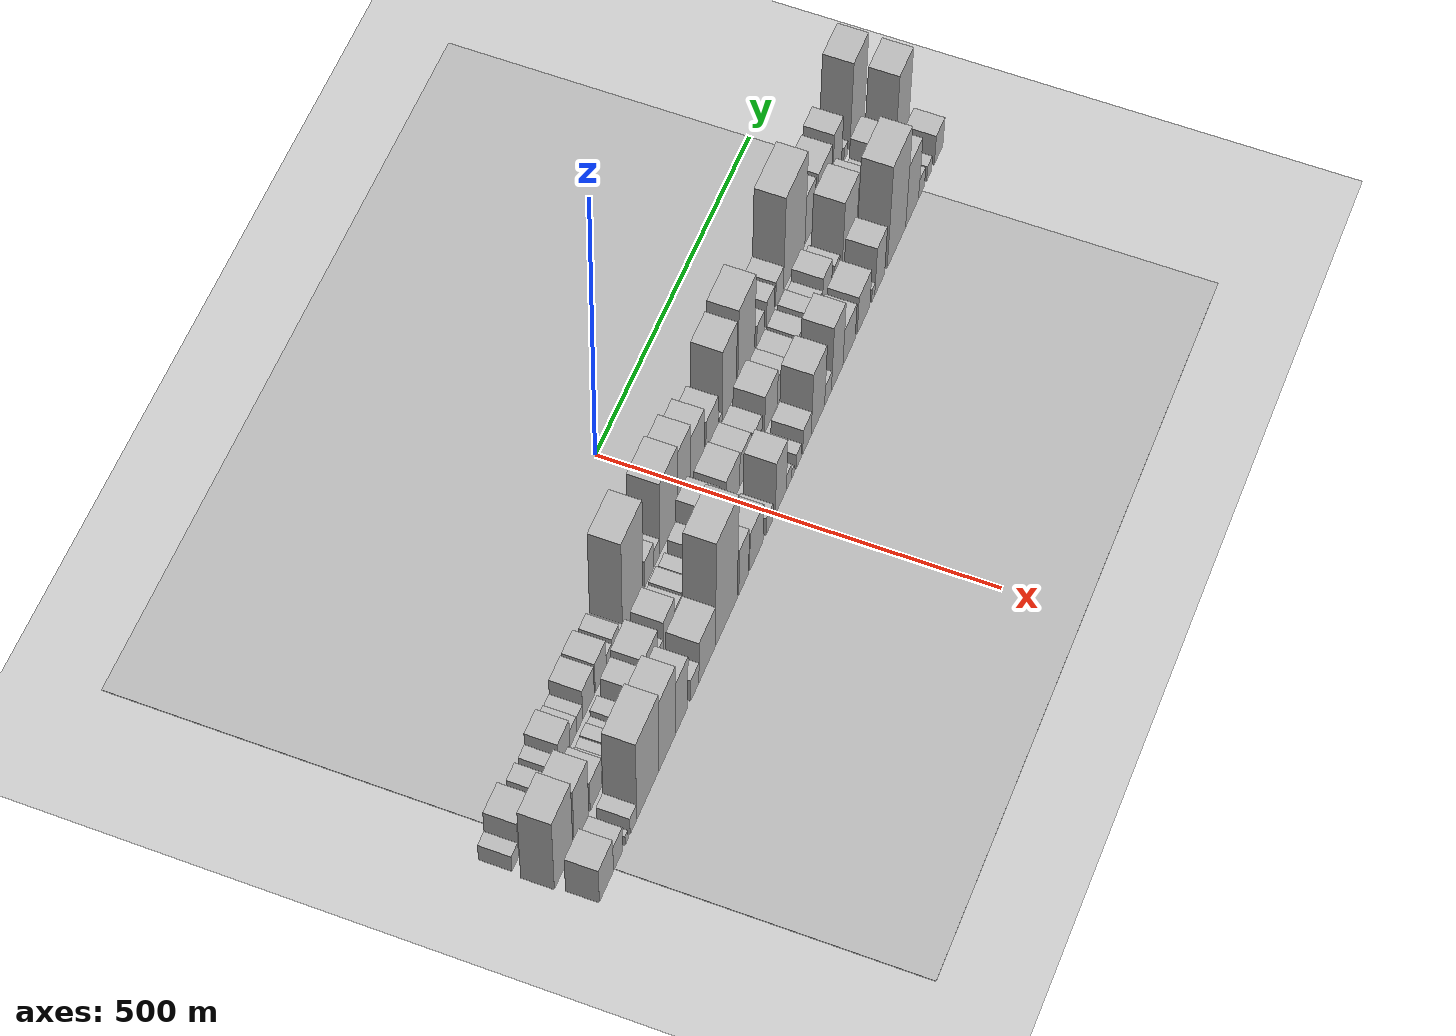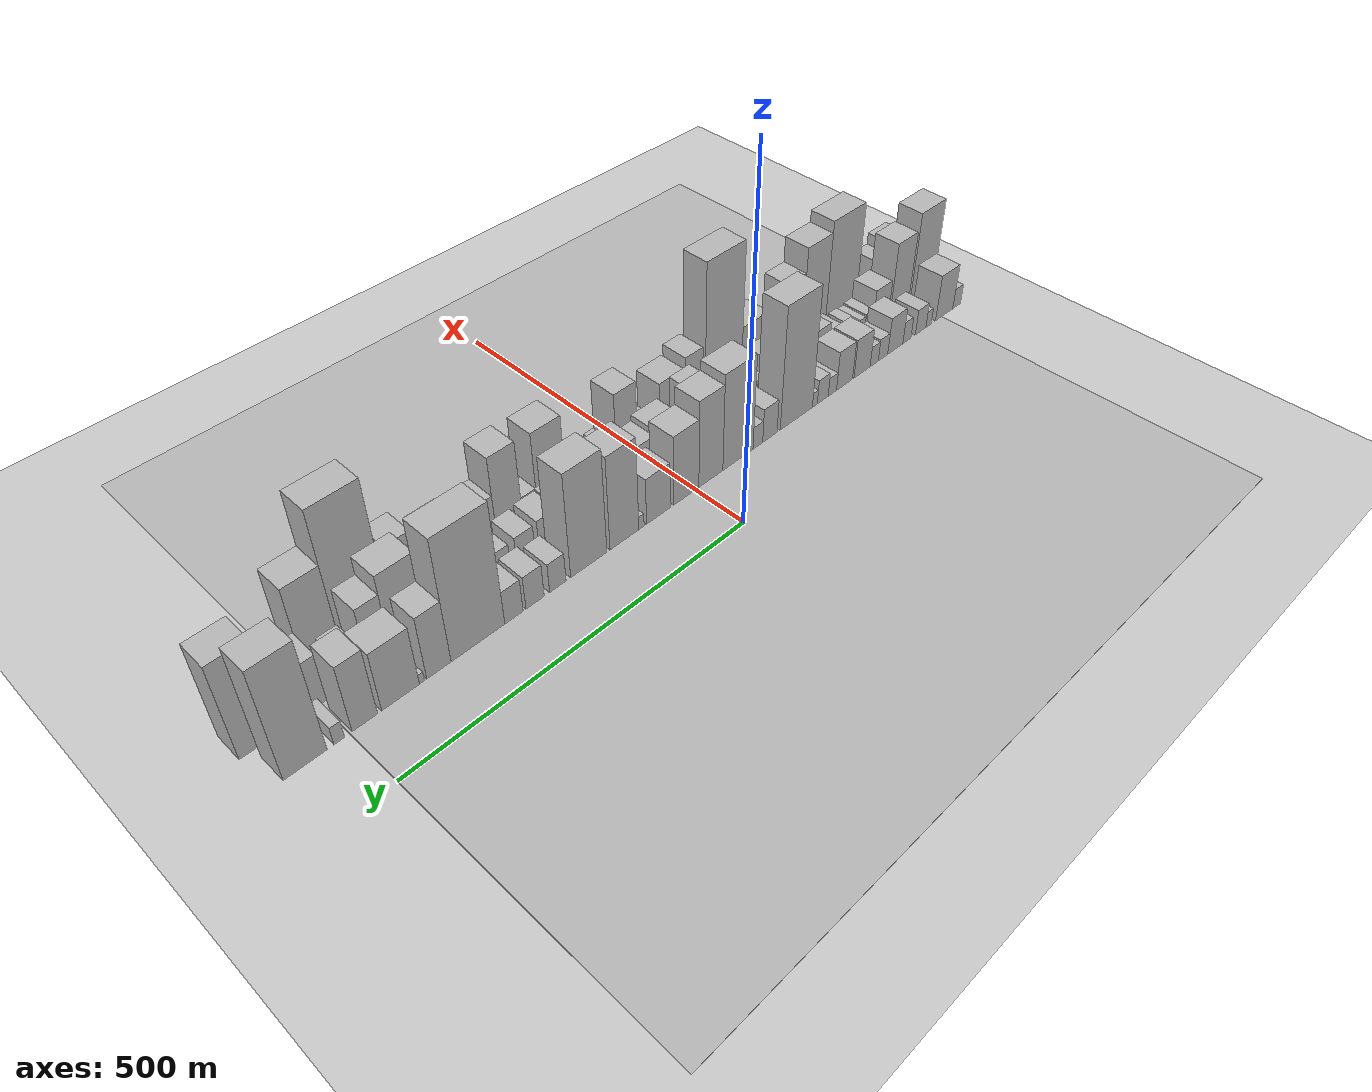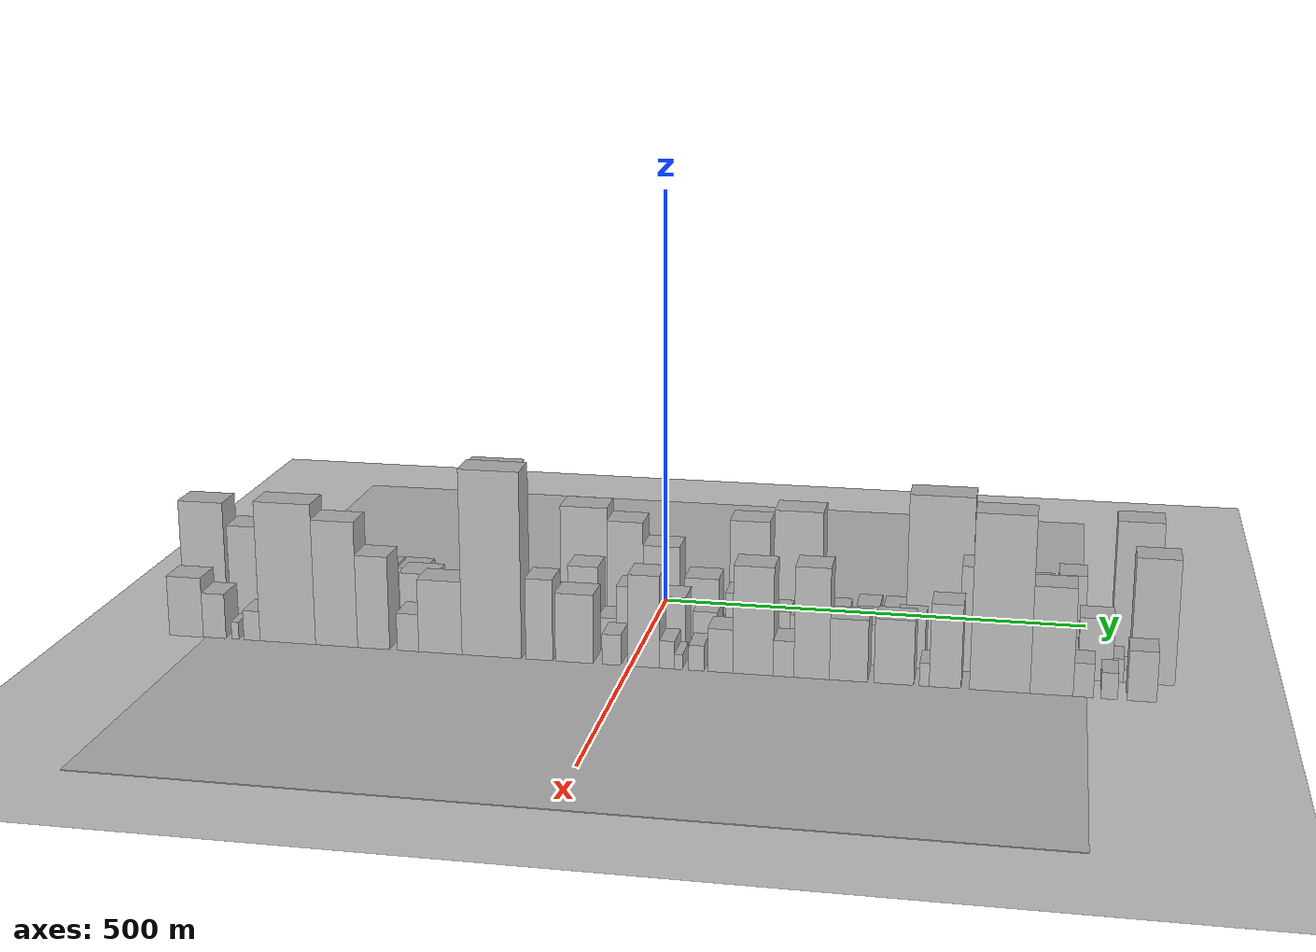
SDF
<?xml version="1.0" encoding="utf-8"?>

<sdf version="1.6">

   <world name="default">

      <gui fullscreen="0">

         <camera name="user_camera">

            <pose>-15 0 4.57585 0 0 0</pose>

            <view_controller>orbit</view_controller>

         </camera>

      </gui>

      <scene>

         <sky>

           <clouds>

             <speed>12</speed>

           </clouds>

         </sky>

         <ambient>0.4 0.4 0.4 1</ambient>

         <background>0.7 0.7 0.7 1</background>

         <shadows>1</shadows>

      </scene>

      <gravity>0 0 -9.8066</gravity>

      <magnetic_field>6e-06 2.3e-05 -4.2e-05</magnetic_field>

      <physics default="0" name="default_physics" type="ode">

         <ode>

            <solver>

               <type>quick</type>

               <iters>10</iters>

               <sor>1.0</sor>

               <use_dynamic_moi_rescaling>0</use_dynamic_moi_rescaling>

            </solver>

            <constraints>

               <cfm>0</cfm>

               <erp>0.2</erp>

               <contact_max_correcting_vel>100</contact_max_correcting_vel>

               <contact_surface_layer>0.001</contact_surface_layer>

            </constraints>

         </ode>

         <max_step_size>0.004</max_step_size>

         <real_time_factor>1</real_time_factor>

         <real_time_update_rate>250</real_time_update_rate>

      </physics>

      <light name="sun" type="directional">

         <cast_shadows>1</cast_shadows>

         <pose>0 0 10 0 0 0</pose>

         <diffuse>0.8 0.8 0.8 1</diffuse>

         <specular>0.2 0.2 0.2 1</specular>

         <attenuation>

            <range>1000</range>

            <constant>0.9</constant>

            <linear>0.01</linear>

            <quadratic>0.001</quadratic>

         </attenuation>

         <direction>-0.5 0.1 -0.9</direction>

      </light>

      <include>

         <name>ground_plane_1</name>

         <uri>model://HANNAS_ground_plane</uri>

         <pose>0 0 0  0 0 0</pose>

      </include>

      <include>

         <name>ground_plane_2</name>

         <uri>model://HANNAS_ground_plane</uri>

         <pose>100 0 0  0 0 0</pose>

      </include>

      <model name="building_1">

         <static>1</static>

         <pose frame="">100.0000 -534.6600 0 0.000000 0.000000 0.000000</pose>

         <link name="link">

            <pose frame="">0 0 16.50 0 0 0</pose>

            <collision name="collision">

               <geometry>

                  <box>

                     <size>40.0000 18.6801 33.0000</size>

                  </box>

               </geometry>

               <max_contacts>10</max_contacts>

               <surface>

                  <contact>

                     <ode/>

                  </contact>

                  <bounce/>

                  <friction>

                     <torsional>

                        <ode/>

                     </torsional>

                     <ode/>

                  </friction>

               </surface>

            </collision>

            <visual name="visual">

               <cast_shadows>0</cast_shadows>

               <geometry>

                  <box>

                     <size>40.0000 18.6801 33.0000</size>

                  </box>

               </geometry>

               <material>

                  <script>

                     <uri>model://HANNAS_wall/materials/scripts</uri>

                     <uri>model://HANNAS_wall/materials/textures</uri>

                     <name>vrc/HANNAS_wall</name>

                  </script>

               </material>

            </visual>

            <self_collide>0</self_collide>

            <enable_wind>0</enable_wind>

            <kinematic>0</kinematic>

         </link>

      </model>

      <model name="building_2">

         <static>1</static>

         <pose frame="">100.0000 -504.8349 0 0.000000 0.000000 0.000000</pose>

         <link name="link">

            <pose frame="">0 0 37.50 0 0 0</pose>

            <collision name="collision">

               <geometry>

                  <box>

                     <size>40.0000 40.9701 75.0000</size>

                  </box>

               </geometry>

               <max_contacts>10</max_contacts>

               <surface>

                  <contact>

                     <ode/>

                  </contact>

                  <bounce/>

                  <friction>

                     <torsional>

                        <ode/>

                     </torsional>

                     <ode/>

                  </friction>

               </surface>

            </collision>

            <visual name="visual">

               <cast_shadows>0</cast_shadows>

               <geometry>

                  <box>

                     <size>40.0000 40.9701 75.0000</size>

                  </box>

               </geometry>

               <material>

                  <script>

                     <uri>model://HANNAS_wall/materials/scripts</uri>

                     <uri>model://HANNAS_wall/materials/textures</uri>

                     <name>vrc/HANNAS_wall</name>

                  </script>

               </material>

            </visual>

            <self_collide>0</self_collide>

            <enable_wind>0</enable_wind>

            <kinematic>0</kinematic>

         </link>

      </model>

      <model name="building_3">

         <static>1</static>

         <pose frame="">100.0000 -468.0988 0 0.000000 0.000000 0.000000</pose>

         <link name="link">

            <pose frame="">0 0 13.50 0 0 0</pose>

            <collision name="collision">

               <geometry>

                  <box>

                     <size>40.0000 12.5020 27.0000</size>

                  </box>

               </geometry>

               <max_contacts>10</max_contacts>

               <surface>

                  <contact>

                     <ode/>

                  </contact>

                  <bounce/>

                  <friction>

                     <torsional>

                        <ode/>

                     </torsional>

                     <ode/>

                  </friction>

               </surface>

            </collision>

            <visual name="visual">

               <cast_shadows>0</cast_shadows>

               <geometry>

                  <box>

                     <size>40.0000 12.5020 27.0000</size>

                  </box>

               </geometry>

               <material>

                  <script>

                     <uri>model://HANNAS_wall/materials/scripts</uri>

                     <uri>model://HANNAS_wall/materials/textures</uri>

                     <name>vrc/HANNAS_wall</name>

                  </script>

               </material>

            </visual>

            <self_collide>0</self_collide>

            <enable_wind>0</enable_wind>

            <kinematic>0</kinematic>

         </link>

      </model>

      <model name="building_4">

         <static>1</static>

         <pose frame="">100.0000 -449.6808 0 0.000000 0.000000 0.000000</pose>

         <link name="link">

            <pose frame="">0 0 21.00 0 0 0</pose>

            <collision name="collision">

               <geometry>

                  <box>

                     <size>40.0000 24.3339 42.0000</size>

                  </box>

               </geometry>

               <max_contacts>10</max_contacts>

               <surface>

                  <contact>

                     <ode/>

                  </contact>

                  <bounce/>

                  <friction>

                     <torsional>

                        <ode/>

                     </torsional>

                     <ode/>

                  </friction>

               </surface>

            </collision>

            <visual name="visual">

               <cast_shadows>0</cast_shadows>

               <geometry>

                  <box>

                     <size>40.0000 24.3339 42.0000</size>

                  </box>

               </geometry>

               <material>

                  <script>

                     <uri>model://HANNAS_wall/materials/scripts</uri>

                     <uri>model://HANNAS_wall/materials/textures</uri>

                     <name>vrc/HANNAS_wall</name>

                  </script>

               </material>

            </visual>

            <self_collide>0</self_collide>

            <enable_wind>0</enable_wind>

            <kinematic>0</kinematic>

         </link>

      </model>

      <model name="building_5">

         <static>1</static>

         <pose frame="">100.0000 -418.4018 0 0.000000 0.000000 0.000000</pose>

         <link name="link">

            <pose frame="">0 0 18.00 0 0 0</pose>

            <collision name="collision">

               <geometry>

                  <box>

                     <size>40.0000 18.2242 36.0000</size>

                  </box>

               </geometry>

               <max_contacts>10</max_contacts>

               <surface>

                  <contact>

                     <ode/>

                  </contact>

                  <bounce/>

                  <friction>

                     <torsional>

                        <ode/>

                     </torsional>

                     <ode/>

                  </friction>

               </surface>

            </collision>

            <visual name="visual">

               <cast_shadows>0</cast_shadows>

               <geometry>

                  <box>

                     <size>40.0000 18.2242 36.0000</size>

                  </box>

               </geometry>

               <material>

                  <script>

                     <uri>model://HANNAS_wall/materials/scripts</uri>

                     <uri>model://HANNAS_wall/materials/textures</uri>

                     <name>vrc/HANNAS_wall</name>

                  </script>

               </material>

            </visual>

            <self_collide>0</self_collide>

            <enable_wind>0</enable_wind>

            <kinematic>0</kinematic>

         </link>

      </model>

      <model name="building_6">

         <static>1</static>

         <pose frame="">100.0000 -392.4293 0 0.000000 0.000000 0.000000</pose>

         <link name="link">

            <pose frame="">0 0 30.00 0 0 0</pose>

            <collision name="collision">

               <geometry>

                  <box>

                     <size>40.0000 33.7208 60.0000</size>

                  </box>

               </geometry>

               <max_contacts>10</max_contacts>

               <surface>

                  <contact>

                     <ode/>

                  </contact>

                  <bounce/>

                  <friction>

                     <torsional>

                        <ode/>

                     </torsional>

                     <ode/>

                  </friction>

               </surface>

            </collision>

            <visual name="visual">

               <cast_shadows>0</cast_shadows>

               <geometry>

                  <box>

                     <size>40.0000 33.7208 60.0000</size>

                  </box>

               </geometry>

               <material>

                  <script>

                     <uri>model://HANNAS_wall/materials/scripts</uri>

                     <uri>model://HANNAS_wall/materials/textures</uri>

                     <name>vrc/HANNAS_wall</name>

                  </script>

               </material>

            </visual>

            <self_collide>0</self_collide>

            <enable_wind>0</enable_wind>

            <kinematic>0</kinematic>

         </link>

      </model>

      <model name="building_7">

         <static>1</static>

         <pose frame="">100.0000 -365.3134 0 0.000000 0.000000 0.000000</pose>

         <link name="link">

            <pose frame="">0 0 18.00 0 0 0</pose>

            <collision name="collision">

               <geometry>

                  <box>

                     <size>40.0000 20.5110 36.0000</size>

                  </box>

               </geometry>

               <max_contacts>10</max_contacts>

               <surface>

                  <contact>

                     <ode/>

                  </contact>

                  <bounce/>

                  <friction>

                     <torsional>

                        <ode/>

                     </torsional>

                     <ode/>

                  </friction>

               </surface>

            </collision>

            <visual name="visual">

               <cast_shadows>0</cast_shadows>

               <geometry>

                  <box>

                     <size>40.0000 20.5110 36.0000</size>

                  </box>

               </geometry>

               <material>

                  <script>

                     <uri>model://HANNAS_wall/materials/scripts</uri>

                     <uri>model://HANNAS_wall/materials/textures</uri>

                     <name>vrc/HANNAS_wall</name>

                  </script>

               </material>

            </visual>

            <self_collide>0</self_collide>

            <enable_wind>0</enable_wind>

            <kinematic>0</kinematic>

         </link>

      </model>

      <model name="building_8">

         <static>1</static>

         <pose frame="">100.0000 -346.2104 0 0.000000 0.000000 0.000000</pose>

         <link name="link">

            <pose frame="">0 0 16.50 0 0 0</pose>

            <collision name="collision">

               <geometry>

                  <box>

                     <size>40.0000 17.6951 33.0000</size>

                  </box>

               </geometry>

               <max_contacts>10</max_contacts>

               <surface>

                  <contact>

                     <ode/>

                  </contact>

                  <bounce/>

                  <friction>

                     <torsional>

                        <ode/>

                     </torsional>

                     <ode/>

                  </friction>

               </surface>

            </collision>

            <visual name="visual">

               <cast_shadows>0</cast_shadows>

               <geometry>

                  <box>

                     <size>40.0000 17.6951 33.0000</size>

                  </box>

               </geometry>

               <material>

                  <script>

                     <uri>model://HANNAS_wall/materials/scripts</uri>

                     <uri>model://HANNAS_wall/materials/textures</uri>

                     <name>vrc/HANNAS_wall</name>

                  </script>

               </material>

            </visual>

            <self_collide>0</self_collide>

            <enable_wind>0</enable_wind>

            <kinematic>0</kinematic>

         </link>

      </model>

      <model name="building_9">

         <static>1</static>

         <pose frame="">100.0000 -320.1440 0 0.000000 0.000000 0.000000</pose>

         <link name="link">

            <pose frame="">0 0 31.50 0 0 0</pose>

            <collision name="collision">

               <geometry>

                  <box>

                     <size>40.0000 34.4376 63.0000</size>

                  </box>

               </geometry>

               <max_contacts>10</max_contacts>

               <surface>

                  <contact>

                     <ode/>

                  </contact>

                  <bounce/>

                  <friction>

                     <torsional>

                        <ode/>

                     </torsional>

                     <ode/>

                  </friction>

               </surface>

            </collision>

            <visual name="visual">

               <cast_shadows>0</cast_shadows>

               <geometry>

                  <box>

                     <size>40.0000 34.4376 63.0000</size>

                  </box>

               </geometry>

               <material>

                  <script>

                     <uri>model://HANNAS_wall/materials/scripts</uri>

                     <uri>model://HANNAS_wall/materials/textures</uri>

                     <name>vrc/HANNAS_wall</name>

                  </script>

               </material>

            </visual>

            <self_collide>0</self_collide>

            <enable_wind>0</enable_wind>

            <kinematic>0</kinematic>

         </link>

      </model>

      <model name="building_10">

         <static>1</static>

         <pose frame="">100.0000 -283.2703 0 0.000000 0.000000 0.000000</pose>

         <link name="link">

            <pose frame="">0 0 31.50 0 0 0</pose>

            <collision name="collision">

               <geometry>

                  <box>

                     <size>40.0000 33.3098 63.0000</size>

                  </box>

               </geometry>

               <max_contacts>10</max_contacts>

               <surface>

                  <contact>

                     <ode/>

                  </contact>

                  <bounce/>

                  <friction>

                     <torsional>

                        <ode/>

                     </torsional>

                     <ode/>

                  </friction>

               </surface>

            </collision>

            <visual name="visual">

               <cast_shadows>0</cast_shadows>

               <geometry>

                  <box>

                     <size>40.0000 33.3098 63.0000</size>

                  </box>

               </geometry>

               <material>

                  <script>

                     <uri>model://HANNAS_wall/materials/scripts</uri>

                     <uri>model://HANNAS_wall/materials/textures</uri>

                     <name>vrc/HANNAS_wall</name>

                  </script>

               </material>

            </visual>

            <self_collide>0</self_collide>

            <enable_wind>0</enable_wind>

            <kinematic>0</kinematic>

         </link>

      </model>

      <model name="building_11">

         <static>1</static>

         <pose frame="">100.0000 -258.0686 0 0.000000 0.000000 0.000000</pose>

         <link name="link">

            <pose frame="">0 0 15.00 0 0 0</pose>

            <collision name="collision">

               <geometry>

                  <box>

                     <size>40.0000 17.0937 30.0000</size>

                  </box>

               </geometry>

               <max_contacts>10</max_contacts>

               <surface>

                  <contact>

                     <ode/>

                  </contact>

                  <bounce/>

                  <friction>

                     <torsional>

                        <ode/>

                     </torsional>

                     <ode/>

                  </friction>

               </surface>

            </collision>

            <visual name="visual">

               <cast_shadows>0</cast_shadows>

               <geometry>

                  <box>

                     <size>40.0000 17.0937 30.0000</size>

                  </box>

               </geometry>

               <material>

                  <script>

                     <uri>model://HANNAS_wall/materials/scripts</uri>

                     <uri>model://HANNAS_wall/materials/textures</uri>

                     <name>vrc/HANNAS_wall</name>

                  </script>

               </material>

            </visual>

            <self_collide>0</self_collide>

            <enable_wind>0</enable_wind>

            <kinematic>0</kinematic>

         </link>

      </model>

      <model name="building_12">

         <static>1</static>

         <pose frame="">100.0000 -238.4917 0 0.000000 0.000000 0.000000</pose>

         <link name="link">

            <pose frame="">0 0 19.50 0 0 0</pose>

            <collision name="collision">

               <geometry>

                  <box>

                     <size>40.0000 22.0602 39.0000</size>

                  </box>

               </geometry>

               <max_contacts>10</max_contacts>

               <surface>

                  <contact>

                     <ode/>

                  </contact>

                  <bounce/>

                  <friction>

                     <torsional>

                        <ode/>

                     </torsional>

                     <ode/>

                  </friction>

               </surface>

            </collision>

            <visual name="visual">

               <cast_shadows>0</cast_shadows>

               <geometry>

                  <box>

                     <size>40.0000 22.0602 39.0000</size>

                  </box>

               </geometry>

               <material>

                  <script>

                     <uri>model://HANNAS_wall/materials/scripts</uri>

                     <uri>model://HANNAS_wall/materials/textures</uri>

                     <name>vrc/HANNAS_wall</name>

                  </script>

               </material>

            </visual>

            <self_collide>0</self_collide>

            <enable_wind>0</enable_wind>

            <kinematic>0</kinematic>

         </link>

      </model>

      <model name="building_13">

         <static>1</static>

         <pose frame="">100.0000 -222.4701 0 0.000000 0.000000 0.000000</pose>

         <link name="link">

            <pose frame="">0 0 12.00 0 0 0</pose>

            <collision name="collision">

               <geometry>

                  <box>

                     <size>40.0000 9.9830 24.0000</size>

                  </box>

               </geometry>

               <max_contacts>10</max_contacts>

               <surface>

                  <contact>

                     <ode/>

                  </contact>

                  <bounce/>

                  <friction>

                     <torsional>

                        <ode/>

                     </torsional>

                     <ode/>

                  </friction>

               </surface>

            </collision>

            <visual name="visual">

               <cast_shadows>0</cast_shadows>

               <geometry>

                  <box>

                     <size>40.0000 9.9830 24.0000</size>

                  </box>

               </geometry>

               <material>

                  <script>

                     <uri>model://HANNAS_wall/materials/scripts</uri>

                     <uri>model://HANNAS_wall/materials/textures</uri>

                     <name>vrc/HANNAS_wall</name>

                  </script>

               </material>

            </visual>

            <self_collide>0</self_collide>

            <enable_wind>0</enable_wind>

            <kinematic>0</kinematic>

         </link>

      </model>

      <model name="building_14">

         <static>1</static>

         <pose frame="">100.0000 -185.9911 0 0.000000 0.000000 0.000000</pose>

         <link name="link">

            <pose frame="">0 0 96.00 0 0 0</pose>

            <collision name="collision">

               <geometry>

                  <box>

                     <size>40.0000 62.9750 192.0000</size>

                  </box>

               </geometry>

               <max_contacts>10</max_contacts>

               <surface>

                  <contact>

                     <ode/>

                  </contact>

                  <bounce/>

                  <friction>

                     <torsional>

                        <ode/>

                     </torsional>

                     <ode/>

                  </friction>

               </surface>

            </collision>

            <visual name="visual">

               <cast_shadows>0</cast_shadows>

               <geometry>

                  <box>

                     <size>40.0000 62.9750 192.0000</size>

                  </box>

               </geometry>

               <material>

                  <script>

                     <uri>model://HANNAS_wall/materials/scripts</uri>

                     <uri>model://HANNAS_wall/materials/textures</uri>

                     <name>vrc/HANNAS_wall</name>

                  </script>

               </material>

            </visual>

            <self_collide>0</self_collide>

            <enable_wind>0</enable_wind>

            <kinematic>0</kinematic>

         </link>

      </model>

      <model name="building_15">

         <static>1</static>

         <pose frame="">100.0000 -134.8019 0 0.000000 0.000000 0.000000</pose>

         <link name="link">

            <pose frame="">0 0 27.00 0 0 0</pose>

            <collision name="collision">

               <geometry>

                  <box>

                     <size>40.0000 27.4034 54.0000</size>

                  </box>

               </geometry>

               <max_contacts>10</max_contacts>

               <surface>

                  <contact>

                     <ode/>

                  </contact>

                  <bounce/>

                  <friction>

                     <torsional>

                        <ode/>

                     </torsional>

                     <ode/>

                  </friction>

               </surface>

            </collision>

            <visual name="visual">

               <cast_shadows>0</cast_shadows>

               <geometry>

                  <box>

                     <size>40.0000 27.4034 54.0000</size>

                  </box>

               </geometry>

               <material>

                  <script>

                     <uri>model://HANNAS_wall/materials/scripts</uri>

                     <uri>model://HANNAS_wall/materials/textures</uri>

                     <name>vrc/HANNAS_wall</name>

                  </script>

               </material>

            </visual>

            <self_collide>0</self_collide>

            <enable_wind>0</enable_wind>

            <kinematic>0</kinematic>

         </link>

      </model>

      <model name="building_16">

         <static>1</static>

         <pose frame="">100.0000 -112.0417 0 0.000000 0.000000 0.000000</pose>

         <link name="link">

            <pose frame="">0 0 18.00 0 0 0</pose>

            <collision name="collision">

               <geometry>

                  <box>

                     <size>40.0000 18.1170 36.0000</size>

                  </box>

               </geometry>

               <max_contacts>10</max_contacts>

               <surface>

                  <contact>

                     <ode/>

                  </contact>

                  <bounce/>

                  <friction>

                     <torsional>

                        <ode/>

                     </torsional>

                     <ode/>

                  </friction>

               </surface>

            </collision>

            <visual name="visual">

               <cast_shadows>0</cast_shadows>

               <geometry>

                  <box>

                     <size>40.0000 18.1170 36.0000</size>

                  </box>

               </geometry>

               <material>

                  <script>

                     <uri>model://HANNAS_wall/materials/scripts</uri>

                     <uri>model://HANNAS_wall/materials/textures</uri>

                     <name>vrc/HANNAS_wall</name>

                  </script>

               </material>

            </visual>

            <self_collide>0</self_collide>

            <enable_wind>0</enable_wind>

            <kinematic>0</kinematic>

         </link>

      </model>

      <model name="building_17">

         <static>1</static>

         <pose frame="">100.0000 -75.4628 0 0.000000 0.000000 0.000000</pose>

         <link name="link">

            <pose frame="">0 0 75.00 0 0 0</pose>

            <collision name="collision">

               <geometry>

                  <box>

                     <size>40.0000 55.0407 150.0000</size>

                  </box>

               </geometry>

               <max_contacts>10</max_contacts>

               <surface>

                  <contact>

                     <ode/>

                  </contact>

                  <bounce/>

                  <friction>

                     <torsional>

                        <ode/>

                     </torsional>

                     <ode/>

                  </friction>

               </surface>

            </collision>

            <visual name="visual">

               <cast_shadows>0</cast_shadows>

               <geometry>

                  <box>

                     <size>40.0000 55.0407 150.0000</size>

                  </box>

               </geometry>

               <material>

                  <script>

                     <uri>model://HANNAS_wall/materials/scripts</uri>

                     <uri>model://HANNAS_wall/materials/textures</uri>

                     <name>vrc/HANNAS_wall</name>

                  </script>

               </material>

            </visual>

            <self_collide>0</self_collide>

            <enable_wind>0</enable_wind>

            <kinematic>0</kinematic>

         </link>

      </model>

      <model name="building_18">

         <static>1</static>

         <pose frame="">100.0000 -26.7473 0 0.000000 0.000000 0.000000</pose>

         <link name="link">

            <pose frame="">0 0 67.50 0 0 0</pose>

            <collision name="collision">

               <geometry>

                  <box>

                     <size>40.0000 42.3904 135.0000</size>

                  </box>

               </geometry>

               <max_contacts>10</max_contacts>

               <surface>

                  <contact>

                     <ode/>

                  </contact>

                  <bounce/>

                  <friction>

                     <torsional>

                        <ode/>

                     </torsional>

                     <ode/>

                  </friction>

               </surface>

            </collision>

            <visual name="visual">

               <cast_shadows>0</cast_shadows>

               <geometry>

                  <box>

                     <size>40.0000 42.3904 135.0000</size>

                  </box>

               </geometry>

               <material>

                  <script>

                     <uri>model://HANNAS_wall/materials/scripts</uri>

                     <uri>model://HANNAS_wall/materials/textures</uri>

                     <name>vrc/HANNAS_wall</name>

                  </script>

               </material>

            </visual>

            <self_collide>0</self_collide>

            <enable_wind>0</enable_wind>

            <kinematic>0</kinematic>

         </link>

      </model>

      <model name="building_19">

         <static>1</static>

         <pose frame="">100.0000 15.9065 0 0.000000 0.000000 0.000000</pose>

         <link name="link">

            <pose frame="">0 0 54.00 0 0 0</pose>

            <collision name="collision">

               <geometry>

                  <box>

                     <size>40.0000 42.9172 108.0000</size>

                  </box>

               </geometry>

               <max_contacts>10</max_contacts>

               <surface>

                  <contact>

                     <ode/>

                  </contact>

                  <bounce/>

                  <friction>

                     <torsional>

                        <ode/>

                     </torsional>

                     <ode/>

                  </friction>

               </surface>

            </collision>

            <visual name="visual">

               <cast_shadows>0</cast_shadows>

               <geometry>

                  <box>

                     <size>40.0000 42.9172 108.0000</size>

                  </box>

               </geometry>

               <material>

                  <script>

                     <uri>model://HANNAS_wall/materials/scripts</uri>

                     <uri>model://HANNAS_wall/materials/textures</uri>

                     <name>vrc/HANNAS_wall</name>

                  </script>

               </material>

            </visual>

            <self_collide>0</self_collide>

            <enable_wind>0</enable_wind>

            <kinematic>0</kinematic>

         </link>

      </model>

      <model name="building_20">

         <static>1</static>

         <pose frame="">100.0000 63.1172 0 0.000000 0.000000 0.000000</pose>

         <link name="link">

            <pose frame="">0 0 36.00 0 0 0</pose>

            <collision name="collision">

               <geometry>

                  <box>

                     <size>40.0000 39.5042 72.0000</size>

                  </box>

               </geometry>

               <max_contacts>10</max_contacts>

               <surface>

                  <contact>

                     <ode/>

                  </contact>

                  <bounce/>

                  <friction>

                     <torsional>

                        <ode/>

                     </torsional>

                     <ode/>

                  </friction>

               </surface>

            </collision>

            <visual name="visual">

               <cast_shadows>0</cast_shadows>

               <geometry>

                  <box>

                     <size>40.0000 39.5042 72.0000</size>

                  </box>

               </geometry>

               <material>

                  <script>

                     <uri>model://HANNAS_wall/materials/scripts</uri>

                     <uri>model://HANNAS_wall/materials/textures</uri>

                     <name>vrc/HANNAS_wall</name>

                  </script>

               </material>

            </visual>

            <self_collide>0</self_collide>

            <enable_wind>0</enable_wind>

            <kinematic>0</kinematic>

         </link>

      </model>

      <model name="building_21">

         <static>1</static>

         <pose frame="">100.0000 91.1646 0 0.000000 0.000000 0.000000</pose>

         <link name="link">

            <pose frame="">0 0 10.50 0 0 0</pose>

            <collision name="collision">

               <geometry>

                  <box>

                     <size>40.0000 8.5904 21.0000</size>

                  </box>

               </geometry>

               <max_contacts>10</max_contacts>

               <surface>

                  <contact>

                     <ode/>

                  </contact>

                  <bounce/>

                  <friction>

                     <torsional>

                        <ode/>

                     </torsional>

                     <ode/>

                  </friction>

               </surface>

            </collision>

            <visual name="visual">

               <cast_shadows>0</cast_shadows>

               <geometry>

                  <box>

                     <size>40.0000 8.5904 21.0000</size>

                  </box>

               </geometry>

               <material>

                  <script>

                     <uri>model://HANNAS_wall/materials/scripts</uri>

                     <uri>model://HANNAS_wall/materials/textures</uri>

                     <name>vrc/HANNAS_wall</name>

                  </script>

               </material>

            </visual>

            <self_collide>0</self_collide>

            <enable_wind>0</enable_wind>

            <kinematic>0</kinematic>

         </link>

      </model>

      <model name="building_22">

         <static>1</static>

         <pose frame="">100.0000 118.4998 0 0.000000 0.000000 0.000000</pose>

         <link name="link">

            <pose frame="">0 0 72.00 0 0 0</pose>

            <collision name="collision">

               <geometry>

                  <box>

                     <size>40.0000 46.0801 144.0000</size>

                  </box>

               </geometry>

               <max_contacts>10</max_contacts>

               <surface>

                  <contact>

                     <ode/>

                  </contact>

                  <bounce/>

                  <friction>

                     <torsional>

                        <ode/>

                     </torsional>

                     <ode/>

                  </friction>

               </surface>

            </collision>

            <visual name="visual">

               <cast_shadows>0</cast_shadows>

               <geometry>

                  <box>

                     <size>40.0000 46.0801 144.0000</size>

                  </box>

               </geometry>

               <material>

                  <script>

                     <uri>model://HANNAS_wall/materials/scripts</uri>

                     <uri>model://HANNAS_wall/materials/textures</uri>

                     <name>vrc/HANNAS_wall</name>

                  </script>

               </material>

            </visual>

            <self_collide>0</self_collide>

            <enable_wind>0</enable_wind>

            <kinematic>0</kinematic>

         </link>

      </model>

      <model name="building_23">

         <static>1</static>

         <pose frame="">100.0000 174.3780 0 0.000000 0.000000 0.000000</pose>

         <link name="link">

            <pose frame="">0 0 79.50 0 0 0</pose>

            <collision name="collision">

               <geometry>

                  <box>

                     <size>40.0000 55.6762 159.0000</size>

                  </box>

               </geometry>

               <max_contacts>10</max_contacts>

               <surface>

                  <contact>

                     <ode/>

                  </contact>

                  <bounce/>

                  <friction>

                     <torsional>

                        <ode/>

                     </torsional>

                     <ode/>

                  </friction>

               </surface>

            </collision>

            <visual name="visual">

               <cast_shadows>0</cast_shadows>

               <geometry>

                  <box>

                     <size>40.0000 55.6762 159.0000</size>

                  </box>

               </geometry>

               <material>

                  <script>

                     <uri>model://HANNAS_wall/materials/scripts</uri>

                     <uri>model://HANNAS_wall/materials/textures</uri>

                     <name>vrc/HANNAS_wall</name>

                  </script>

               </material>

            </visual>

            <self_collide>0</self_collide>

            <enable_wind>0</enable_wind>

            <kinematic>0</kinematic>

         </link>

      </model>

      <model name="building_24">

         <static>1</static>

         <pose frame="">100.0000 221.4024 0 0.000000 0.000000 0.000000</pose>

         <link name="link">

            <pose frame="">0 0 22.50 0 0 0</pose>

            <collision name="collision">

               <geometry>

                  <box>

                     <size>40.0000 24.3726 45.0000</size>

                  </box>

               </geometry>

               <max_contacts>10</max_contacts>

               <surface>

                  <contact>

                     <ode/>

                  </contact>

                  <bounce/>

                  <friction>

                     <torsional>

                        <ode/>

                     </torsional>

                     <ode/>

                  </friction>

               </surface>

            </collision>

            <visual name="visual">

               <cast_shadows>0</cast_shadows>

               <geometry>

                  <box>

                     <size>40.0000 24.3726 45.0000</size>

                  </box>

               </geometry>

               <material>

                  <script>

                     <uri>model://HANNAS_wall/materials/scripts</uri>

                     <uri>model://HANNAS_wall/materials/textures</uri>

                     <name>vrc/HANNAS_wall</name>

                  </script>

               </material>

            </visual>

            <self_collide>0</self_collide>

            <enable_wind>0</enable_wind>

            <kinematic>0</kinematic>

         </link>

      </model>

      <model name="building_25">

         <static>1</static>

         <pose frame="">100.0000 254.8437 0 0.000000 0.000000 0.000000</pose>

         <link name="link">

            <pose frame="">0 0 25.50 0 0 0</pose>

            <collision name="collision">

               <geometry>

                  <box>

                     <size>40.0000 26.5101 51.0000</size>

                  </box>

               </geometry>

               <max_contacts>10</max_contacts>

               <surface>

                  <contact>

                     <ode/>

                  </contact>

                  <bounce/>

                  <friction>

                     <torsional>

                        <ode/>

                     </torsional>

                     <ode/>

                  </friction>

               </surface>

            </collision>

            <visual name="visual">

               <cast_shadows>0</cast_shadows>

               <geometry>

                  <box>

                     <size>40.0000 26.5101 51.0000</size>

                  </box>

               </geometry>

               <material>

                  <script>

                     <uri>model://HANNAS_wall/materials/scripts</uri>

                     <uri>model://HANNAS_wall/materials/textures</uri>

                     <name>vrc/HANNAS_wall</name>

                  </script>

               </material>

            </visual>

            <self_collide>0</self_collide>

            <enable_wind>0</enable_wind>

            <kinematic>0</kinematic>

         </link>

      </model>

      <model name="building_26">

         <static>1</static>

         <pose frame="">100.0000 285.0551 0 0.000000 0.000000 0.000000</pose>

         <link name="link">

            <pose frame="">0 0 25.50 0 0 0</pose>

            <collision name="collision">

               <geometry>

                  <box>

                     <size>40.0000 25.9128 51.0000</size>

                  </box>

               </geometry>

               <max_contacts>10</max_contacts>

               <surface>

                  <contact>

                     <ode/>

                  </contact>

                  <bounce/>

                  <friction>

                     <torsional>

                        <ode/>

                     </torsional>

                     <ode/>

                  </friction>

               </surface>

            </collision>

            <visual name="visual">

               <cast_shadows>0</cast_shadows>

               <geometry>

                  <box>

                     <size>40.0000 25.9128 51.0000</size>

                  </box>

               </geometry>

               <material>

                  <script>

                     <uri>model://HANNAS_wall/materials/scripts</uri>

                     <uri>model://HANNAS_wall/materials/textures</uri>

                     <name>vrc/HANNAS_wall</name>

                  </script>

               </material>

            </visual>

            <self_collide>0</self_collide>

            <enable_wind>0</enable_wind>

            <kinematic>0</kinematic>

         </link>

      </model>

      <model name="building_27">

         <static>1</static>

         <pose frame="">100.0000 334.7470 0 0.000000 0.000000 0.000000</pose>

         <link name="link">

            <pose frame="">0 0 93.00 0 0 0</pose>

            <collision name="collision">

               <geometry>

                  <box>

                     <size>40.0000 73.4709 186.0000</size>

                  </box>

               </geometry>

               <max_contacts>10</max_contacts>

               <surface>

                  <contact>

                     <ode/>

                  </contact>

                  <bounce/>

                  <friction>

                     <torsional>

                        <ode/>

                     </torsional>

                     <ode/>

                  </friction>

               </surface>

            </collision>

            <visual name="visual">

               <cast_shadows>0</cast_shadows>

               <geometry>

                  <box>

                     <size>40.0000 73.4709 186.0000</size>

                  </box>

               </geometry>

               <material>

                  <script>

                     <uri>model://HANNAS_wall/materials/scripts</uri>

                     <uri>model://HANNAS_wall/materials/textures</uri>

                     <name>vrc/HANNAS_wall</name>

                  </script>

               </material>

            </visual>

            <self_collide>0</self_collide>

            <enable_wind>0</enable_wind>

            <kinematic>0</kinematic>

         </link>

      </model>

      <model name="building_28">

         <static>1</static>

         <pose frame="">100.0000 387.5578 0 0.000000 0.000000 0.000000</pose>

         <link name="link">

            <pose frame="">0 0 48.00 0 0 0</pose>

            <collision name="collision">

               <geometry>

                  <box>

                     <size>40.0000 32.1508 96.0000</size>

                  </box>

               </geometry>

               <max_contacts>10</max_contacts>

               <surface>

                  <contact>

                     <ode/>

                  </contact>

                  <bounce/>

                  <friction>

                     <torsional>

                        <ode/>

                     </torsional>

                     <ode/>

                  </friction>

               </surface>

            </collision>

            <visual name="visual">

               <cast_shadows>0</cast_shadows>

               <geometry>

                  <box>

                     <size>40.0000 32.1508 96.0000</size>

                  </box>

               </geometry>

               <material>

                  <script>

                     <uri>model://HANNAS_wall/materials/scripts</uri>

                     <uri>model://HANNAS_wall/materials/textures</uri>

                     <name>vrc/HANNAS_wall</name>

                  </script>

               </material>

            </visual>

            <self_collide>0</self_collide>

            <enable_wind>0</enable_wind>

            <kinematic>0</kinematic>

         </link>

      </model>

      <model name="building_29">

         <static>1</static>

         <pose frame="">100.0000 409.8102 0 0.000000 0.000000 0.000000</pose>

         <link name="link">

            <pose frame="">0 0 7.50 0 0 0</pose>

            <collision name="collision">

               <geometry>

                  <box>

                     <size>40.0000 6.3538 15.0000</size>

                  </box>

               </geometry>

               <max_contacts>10</max_contacts>

               <surface>

                  <contact>

                     <ode/>

                  </contact>

                  <bounce/>

                  <friction>

                     <torsional>

                        <ode/>

                     </torsional>

                     <ode/>

                  </friction>

               </surface>

            </collision>

            <visual name="visual">

               <cast_shadows>0</cast_shadows>

               <geometry>

                  <box>

                     <size>40.0000 6.3538 15.0000</size>

                  </box>

               </geometry>

               <material>

                  <script>

                     <uri>model://HANNAS_wall/materials/scripts</uri>

                     <uri>model://HANNAS_wall/materials/textures</uri>

                     <name>vrc/HANNAS_wall</name>

                  </script>

               </material>

            </visual>

            <self_collide>0</self_collide>

            <enable_wind>0</enable_wind>

            <kinematic>0</kinematic>

         </link>

      </model>

      <model name="building_30">

         <static>1</static>

         <pose frame="">100.0000 436.9131 0 0.000000 0.000000 0.000000</pose>

         <link name="link">

            <pose frame="">0 0 45.00 0 0 0</pose>

            <collision name="collision">

               <geometry>

                  <box>

                     <size>40.0000 47.8520 90.0000</size>

                  </box>

               </geometry>

               <max_contacts>10</max_contacts>

               <surface>

                  <contact>

                     <ode/>

                  </contact>

                  <bounce/>

                  <friction>

                     <torsional>

                        <ode/>

                     </torsional>

                     <ode/>

                  </friction>

               </surface>

            </collision>

            <visual name="visual">

               <cast_shadows>0</cast_shadows>

               <geometry>

                  <box>

                     <size>40.0000 47.8520 90.0000</size>

                  </box>

               </geometry>

               <material>

                  <script>

                     <uri>model://HANNAS_wall/materials/scripts</uri>

                     <uri>model://HANNAS_wall/materials/textures</uri>

                     <name>vrc/HANNAS_wall</name>

                  </script>

               </material>

            </visual>

            <self_collide>0</self_collide>

            <enable_wind>0</enable_wind>

            <kinematic>0</kinematic>

         </link>

      </model>

      <model name="building_31">

         <static>1</static>

         <pose frame="">100.0000 481.4354 0 0.000000 0.000000 0.000000</pose>

         <link name="link">

            <pose frame="">0 0 51.00 0 0 0</pose>

            <collision name="collision">

               <geometry>

                  <box>

                     <size>40.0000 31.1927 102.0000</size>

                  </box>

               </geometry>

               <max_contacts>10</max_contacts>

               <surface>

                  <contact>

                     <ode/>

                  </contact>

                  <bounce/>

                  <friction>

                     <torsional>

                        <ode/>

                     </torsional>

                     <ode/>

                  </friction>

               </surface>

            </collision>

            <visual name="visual">

               <cast_shadows>0</cast_shadows>

               <geometry>

                  <box>

                     <size>40.0000 31.1927 102.0000</size>

                  </box>

               </geometry>

               <material>

                  <script>

                     <uri>model://HANNAS_wall/materials/scripts</uri>

                     <uri>model://HANNAS_wall/materials/textures</uri>

                     <name>vrc/HANNAS_wall</name>

                  </script>

               </material>

            </visual>

            <self_collide>0</self_collide>

            <enable_wind>0</enable_wind>

            <kinematic>0</kinematic>

         </link>

      </model>

      <model name="building_32">

         <static>1</static>

         <pose frame="">100.0000 512.4188 0 0.000000 0.000000 0.000000</pose>

         <link name="link">

            <pose frame="">0 0 13.50 0 0 0</pose>

            <collision name="collision">

               <geometry>

                  <box>

                     <size>40.0000 12.7741 27.0000</size>

                  </box>

               </geometry>

               <max_contacts>10</max_contacts>

               <surface>

                  <contact>

                     <ode/>

                  </contact>

                  <bounce/>

                  <friction>

                     <torsional>

                        <ode/>

                     </torsional>

                     <ode/>

                  </friction>

               </surface>

            </collision>

            <visual name="visual">

               <cast_shadows>0</cast_shadows>

               <geometry>

                  <box>

                     <size>40.0000 12.7741 27.0000</size>

                  </box>

               </geometry>

               <material>

                  <script>

                     <uri>model://HANNAS_wall/materials/scripts</uri>

                     <uri>model://HANNAS_wall/materials/textures</uri>

                     <name>vrc/HANNAS_wall</name>

                  </script>

               </material>

            </visual>

            <self_collide>0</self_collide>

            <enable_wind>0</enable_wind>

            <kinematic>0</kinematic>

         </link>

      </model>

      <model name="building_33">

         <static>1</static>

         <pose frame="">100.0000 552.2329 0 0.000000 0.000000 0.000000</pose>

         <link name="link">

            <pose frame="">0 0 84.00 0 0 0</pose>

            <collision name="collision">

               <geometry>

                  <box>

                     <size>40.0000 50.8540 168.0000</size>

                  </box>

               </geometry>

               <max_contacts>10</max_contacts>

               <surface>

                  <contact>

                     <ode/>

                  </contact>

                  <bounce/>

                  <friction>

                     <torsional>

                        <ode/>

                     </torsional>

                     <ode/>

                  </friction>

               </surface>

            </collision>

            <visual name="visual">

               <cast_shadows>0</cast_shadows>

               <geometry>

                  <box>

                     <size>40.0000 50.8540 168.0000</size>

                  </box>

               </geometry>

               <material>

                  <script>

                     <uri>model://HANNAS_wall/materials/scripts</uri>

                     <uri>model://HANNAS_wall/materials/textures</uri>

                     <name>vrc/HANNAS_wall</name>

                  </script>

               </material>

            </visual>

            <self_collide>0</self_collide>

            <enable_wind>0</enable_wind>

            <kinematic>0</kinematic>

         </link>

      </model>

      <model name="building_34">

         <static>1</static>

         <pose frame="">152.0000 -520.9492 0 0.000000 0.000000 0.000000</pose>

         <link name="link">

            <pose frame="">0 0 73.50 0 0 0</pose>

            <collision name="collision">

               <geometry>

                  <box>

                     <size>40.0000 54.1016 147.0000</size>

                  </box>

               </geometry>

               <max_contacts>10</max_contacts>

               <surface>

                  <contact>

                     <ode/>

                  </contact>

                  <bounce/>

                  <friction>

                     <torsional>

                        <ode/>

                     </torsional>

                     <ode/>

                  </friction>

               </surface>

            </collision>

            <visual name="visual">

               <cast_shadows>0</cast_shadows>

               <geometry>

                  <box>

                     <size>40.0000 54.1016 147.0000</size>

                  </box>

               </geometry>

               <material>

                  <script>

                     <uri>model://HANNAS_wall/materials/scripts</uri>

                     <uri>model://HANNAS_wall/materials/textures</uri>

                     <name>vrc/HANNAS_wall</name>

                  </script>

               </material>

            </visual>

            <self_collide>0</self_collide>

            <enable_wind>0</enable_wind>

            <kinematic>0</kinematic>

         </link>

      </model>

      <model name="building_35">

         <static>1</static>

         <pose frame="">152.0000 -468.5705 0 0.000000 0.000000 0.000000</pose>

         <link name="link">

            <pose frame="">0 0 60.00 0 0 0</pose>

            <collision name="collision">

               <geometry>

                  <box>

                     <size>40.0000 42.6557 120.0000</size>

                  </box>

               </geometry>

               <max_contacts>10</max_contacts>

               <surface>

                  <contact>

                     <ode/>

                  </contact>

                  <bounce/>

                  <friction>

                     <torsional>

                        <ode/>

                     </torsional>

                     <ode/>

                  </friction>

               </surface>

            </collision>

            <visual name="visual">

               <cast_shadows>0</cast_shadows>

               <geometry>

                  <box>

                     <size>40.0000 42.6557 120.0000</size>

                  </box>

               </geometry>

               <material>

                  <script>

                     <uri>model://HANNAS_wall/materials/scripts</uri>

                     <uri>model://HANNAS_wall/materials/textures</uri>

                     <name>vrc/HANNAS_wall</name>

                  </script>

               </material>

            </visual>

            <self_collide>0</self_collide>

            <enable_wind>0</enable_wind>

            <kinematic>0</kinematic>

         </link>

      </model>

      <model name="building_36">

         <static>1</static>

         <pose frame="">152.0000 -425.7523 0 0.000000 0.000000 0.000000</pose>

         <link name="link">

            <pose frame="">0 0 31.50 0 0 0</pose>

            <collision name="collision">

               <geometry>

                  <box>

                     <size>40.0000 34.9807 63.0000</size>

                  </box>

               </geometry>

               <max_contacts>10</max_contacts>

               <surface>

                  <contact>

                     <ode/>

                  </contact>

                  <bounce/>

                  <friction>

                     <torsional>

                        <ode/>

                     </torsional>

                     <ode/>

                  </friction>

               </surface>

            </collision>

            <visual name="visual">

               <cast_shadows>0</cast_shadows>

               <geometry>

                  <box>

                     <size>40.0000 34.9807 63.0000</size>

                  </box>

               </geometry>

               <material>

                  <script>

                     <uri>model://HANNAS_wall/materials/scripts</uri>

                     <uri>model://HANNAS_wall/materials/textures</uri>

                     <name>vrc/HANNAS_wall</name>

                  </script>

               </material>

            </visual>

            <self_collide>0</self_collide>

            <enable_wind>0</enable_wind>

            <kinematic>0</kinematic>

         </link>

      </model>

      <model name="building_37">

         <static>1</static>

         <pose frame="">152.0000 -399.0803 0 0.000000 0.000000 0.000000</pose>

         <link name="link">

            <pose frame="">0 0 16.50 0 0 0</pose>

            <collision name="collision">

               <geometry>

                  <box>

                     <size>40.0000 18.3633 33.0000</size>

                  </box>

               </geometry>

               <max_contacts>10</max_contacts>

               <surface>

                  <contact>

                     <ode/>

                  </contact>

                  <bounce/>

                  <friction>

                     <torsional>

                        <ode/>

                     </torsional>

                     <ode/>

                  </friction>

               </surface>

            </collision>

            <visual name="visual">

               <cast_shadows>0</cast_shadows>

               <geometry>

                  <box>

                     <size>40.0000 18.3633 33.0000</size>

                  </box>

               </geometry>

               <material>

                  <script>

                     <uri>model://HANNAS_wall/materials/scripts</uri>

                     <uri>model://HANNAS_wall/materials/textures</uri>

                     <name>vrc/HANNAS_wall</name>

                  </script>

               </material>

            </visual>

            <self_collide>0</self_collide>

            <enable_wind>0</enable_wind>

            <kinematic>0</kinematic>

         </link>

      </model>

      <model name="building_38">

         <static>1</static>

         <pose frame="">152.0000 -382.2008 0 0.000000 0.000000 0.000000</pose>

         <link name="link">

            <pose frame="">0 0 15.00 0 0 0</pose>

            <collision name="collision">

               <geometry>

                  <box>

                     <size>40.0000 15.3959 30.0000</size>

                  </box>

               </geometry>

               <max_contacts>10</max_contacts>

               <surface>

                  <contact>

                     <ode/>

                  </contact>

                  <bounce/>

                  <friction>

                     <torsional>

                        <ode/>

                     </torsional>

                     <ode/>

                  </friction>

               </surface>

            </collision>

            <visual name="visual">

               <cast_shadows>0</cast_shadows>

               <geometry>

                  <box>

                     <size>40.0000 15.3959 30.0000</size>

                  </box>

               </geometry>

               <material>

                  <script>

                     <uri>model://HANNAS_wall/materials/scripts</uri>

                     <uri>model://HANNAS_wall/materials/textures</uri>

                     <name>vrc/HANNAS_wall</name>

                  </script>

               </material>

            </visual>

            <self_collide>0</self_collide>

            <enable_wind>0</enable_wind>

            <kinematic>0</kinematic>

         </link>

      </model>

      <model name="building_39">

         <static>1</static>

         <pose frame="">152.0000 -365.5095 0 0.000000 0.000000 0.000000</pose>

         <link name="link">

            <pose frame="">0 0 16.50 0 0 0</pose>

            <collision name="collision">

               <geometry>

                  <box>

                     <size>40.0000 17.9867 33.0000</size>

                  </box>

               </geometry>

               <max_contacts>10</max_contacts>

               <surface>

                  <contact>

                     <ode/>

                  </contact>

                  <bounce/>

                  <friction>

                     <torsional>

                        <ode/>

                     </torsional>

                     <ode/>

                  </friction>

               </surface>

            </collision>

            <visual name="visual">

               <cast_shadows>0</cast_shadows>

               <geometry>

                  <box>

                     <size>40.0000 17.9867 33.0000</size>

                  </box>

               </geometry>

               <material>

                  <script>

                     <uri>model://HANNAS_wall/materials/scripts</uri>

                     <uri>model://HANNAS_wall/materials/textures</uri>

                     <name>vrc/HANNAS_wall</name>

                  </script>

               </material>

            </visual>

            <self_collide>0</self_collide>

            <enable_wind>0</enable_wind>

            <kinematic>0</kinematic>

         </link>

      </model>

      <model name="building_40">

         <static>1</static>

         <pose frame="">152.0000 -350.2449 0 0.000000 0.000000 0.000000</pose>

         <link name="link">

            <pose frame="">0 0 13.50 0 0 0</pose>

            <collision name="collision">

               <geometry>

                  <box>

                     <size>40.0000 12.5424 27.0000</size>

                  </box>

               </geometry>

               <max_contacts>10</max_contacts>

               <surface>

                  <contact>

                     <ode/>

                  </contact>

                  <bounce/>

                  <friction>

                     <torsional>

                        <ode/>

                     </torsional>

                     <ode/>

                  </friction>

               </surface>

            </collision>

            <visual name="visual">

               <cast_shadows>0</cast_shadows>

               <geometry>

                  <box>

                     <size>40.0000 12.5424 27.0000</size>

                  </box>

               </geometry>

               <material>

                  <script>

                     <uri>model://HANNAS_wall/materials/scripts</uri>

                     <uri>model://HANNAS_wall/materials/textures</uri>

                     <name>vrc/HANNAS_wall</name>

                  </script>

               </material>

            </visual>

            <self_collide>0</self_collide>

            <enable_wind>0</enable_wind>

            <kinematic>0</kinematic>

         </link>

      </model>

      <model name="building_41">

         <static>1</static>

         <pose frame="">152.0000 -333.3056 0 0.000000 0.000000 0.000000</pose>

         <link name="link">

            <pose frame="">0 0 19.50 0 0 0</pose>

            <collision name="collision">

               <geometry>

                  <box>

                     <size>40.0000 21.3363 39.0000</size>

                  </box>

               </geometry>

               <max_contacts>10</max_contacts>

               <surface>

                  <contact>

                     <ode/>

                  </contact>

                  <bounce/>

                  <friction>

                     <torsional>

                        <ode/>

                     </torsional>

                     <ode/>

                  </friction>

               </surface>

            </collision>

            <visual name="visual">

               <cast_shadows>0</cast_shadows>

               <geometry>

                  <box>

                     <size>40.0000 21.3363 39.0000</size>

                  </box>

               </geometry>

               <material>

                  <script>

                     <uri>model://HANNAS_wall/materials/scripts</uri>

                     <uri>model://HANNAS_wall/materials/textures</uri>

                     <name>vrc/HANNAS_wall</name>

                  </script>

               </material>

            </visual>

            <self_collide>0</self_collide>

            <enable_wind>0</enable_wind>

            <kinematic>0</kinematic>

         </link>

      </model>

      <model name="building_42">

         <static>1</static>

         <pose frame="">152.0000 -317.7434 0 0.000000 0.000000 0.000000</pose>

         <link name="link">

            <pose frame="">0 0 10.50 0 0 0</pose>

            <collision name="collision">

               <geometry>

                  <box>

                     <size>40.0000 9.7881 21.0000</size>

                  </box>

               </geometry>

               <max_contacts>10</max_contacts>

               <surface>

                  <contact>

                     <ode/>

                  </contact>

                  <bounce/>

                  <friction>

                     <torsional>

                        <ode/>

                     </torsional>

                     <ode/>

                  </friction>

               </surface>

            </collision>

            <visual name="visual">

               <cast_shadows>0</cast_shadows>

               <geometry>

                  <box>

                     <size>40.0000 9.7881 21.0000</size>

                  </box>

               </geometry>

               <material>

                  <script>

                     <uri>model://HANNAS_wall/materials/scripts</uri>

                     <uri>model://HANNAS_wall/materials/textures</uri>

                     <name>vrc/HANNAS_wall</name>

                  </script>

               </material>

            </visual>

            <self_collide>0</self_collide>

            <enable_wind>0</enable_wind>

            <kinematic>0</kinematic>

         </link>

      </model>

      <model name="building_43">

         <static>1</static>

         <pose frame="">152.0000 -297.5751 0 0.000000 0.000000 0.000000</pose>

         <link name="link">

            <pose frame="">0 0 30.00 0 0 0</pose>

            <collision name="collision">

               <geometry>

                  <box>

                     <size>40.0000 30.5484 60.0000</size>

                  </box>

               </geometry>

               <max_contacts>10</max_contacts>

               <surface>

                  <contact>

                     <ode/>

                  </contact>

                  <bounce/>

                  <friction>

                     <torsional>

                        <ode/>

                     </torsional>

                     <ode/>

                  </friction>

               </surface>

            </collision>

            <visual name="visual">

               <cast_shadows>0</cast_shadows>

               <geometry>

                  <box>

                     <size>40.0000 30.5484 60.0000</size>

                  </box>

               </geometry>

               <material>

                  <script>

                     <uri>model://HANNAS_wall/materials/scripts</uri>

                     <uri>model://HANNAS_wall/materials/textures</uri>

                     <name>vrc/HANNAS_wall</name>

                  </script>

               </material>

            </visual>

            <self_collide>0</self_collide>

            <enable_wind>0</enable_wind>

            <kinematic>0</kinematic>

         </link>

      </model>

      <model name="building_44">

         <static>1</static>

         <pose frame="">152.0000 -260.7096 0 0.000000 0.000000 0.000000</pose>

         <link name="link">

            <pose frame="">0 0 37.50 0 0 0</pose>

            <collision name="collision">

               <geometry>

                  <box>

                     <size>40.0000 43.1825 75.0000</size>

                  </box>

               </geometry>

               <max_contacts>10</max_contacts>

               <surface>

                  <contact>

                     <ode/>

                  </contact>

                  <bounce/>

                  <friction>

                     <torsional>

                        <ode/>

                     </torsional>

                     <ode/>

                  </friction>

               </surface>

            </collision>

            <visual name="visual">

               <cast_shadows>0</cast_shadows>

               <geometry>

                  <box>

                     <size>40.0000 43.1825 75.0000</size>

                  </box>

               </geometry>

               <material>

                  <script>

                     <uri>model://HANNAS_wall/materials/scripts</uri>

                     <uri>model://HANNAS_wall/materials/textures</uri>

                     <name>vrc/HANNAS_wall</name>

                  </script>

               </material>

            </visual>

            <self_collide>0</self_collide>

            <enable_wind>0</enable_wind>

            <kinematic>0</kinematic>

         </link>

      </model>

      <model name="building_45">

         <static>1</static>

         <pose frame="">152.0000 -231.1331 0 0.000000 0.000000 0.000000</pose>

         <link name="link">

            <pose frame="">0 0 15.00 0 0 0</pose>

            <collision name="collision">

               <geometry>

                  <box>

                     <size>40.0000 15.9706 30.0000</size>

                  </box>

               </geometry>

               <max_contacts>10</max_contacts>

               <surface>

                  <contact>

                     <ode/>

                  </contact>

                  <bounce/>

                  <friction>

                     <torsional>

                        <ode/>

                     </torsional>

                     <ode/>

                  </friction>

               </surface>

            </collision>

            <visual name="visual">

               <cast_shadows>0</cast_shadows>

               <geometry>

                  <box>

                     <size>40.0000 15.9706 30.0000</size>

                  </box>

               </geometry>

               <material>

                  <script>

                     <uri>model://HANNAS_wall/materials/scripts</uri>

                     <uri>model://HANNAS_wall/materials/textures</uri>

                     <name>vrc/HANNAS_wall</name>

                  </script>

               </material>

            </visual>

            <self_collide>0</self_collide>

            <enable_wind>0</enable_wind>

            <kinematic>0</kinematic>

         </link>

      </model>

      <model name="building_46">

         <static>1</static>

         <pose frame="">152.0000 -205.4226 0 0.000000 0.000000 0.000000</pose>

         <link name="link">

            <pose frame="">0 0 33.00 0 0 0</pose>

            <collision name="collision">

               <geometry>

                  <box>

                     <size>40.0000 35.4503 66.0000</size>

                  </box>

               </geometry>

               <max_contacts>10</max_contacts>

               <surface>

                  <contact>

                     <ode/>

                  </contact>

                  <bounce/>

                  <friction>

                     <torsional>

                        <ode/>

                     </torsional>

                     <ode/>

                  </friction>

               </surface>

            </collision>

            <visual name="visual">

               <cast_shadows>0</cast_shadows>

               <geometry>

                  <box>

                     <size>40.0000 35.4503 66.0000</size>

                  </box>

               </geometry>

               <material>

                  <script>

                     <uri>model://HANNAS_wall/materials/scripts</uri>

                     <uri>model://HANNAS_wall/materials/textures</uri>

                     <name>vrc/HANNAS_wall</name>

                  </script>

               </material>

            </visual>

            <self_collide>0</self_collide>

            <enable_wind>0</enable_wind>

            <kinematic>0</kinematic>

         </link>

      </model>

      <model name="building_47">

         <static>1</static>

         <pose frame="">152.0000 -177.1141 0 0.000000 0.000000 0.000000</pose>

         <link name="link">

            <pose frame="">0 0 19.50 0 0 0</pose>

            <collision name="collision">

               <geometry>

                  <box>

                     <size>40.0000 21.1668 39.0000</size>

                  </box>

               </geometry>

               <max_contacts>10</max_contacts>

               <surface>

                  <contact>

                     <ode/>

                  </contact>

                  <bounce/>

                  <friction>

                     <torsional>

                        <ode/>

                     </torsional>

                     <ode/>

                  </friction>

               </surface>

            </collision>

            <visual name="visual">

               <cast_shadows>0</cast_shadows>

               <geometry>

                  <box>

                     <size>40.0000 21.1668 39.0000</size>

                  </box>

               </geometry>

               <material>

                  <script>

                     <uri>model://HANNAS_wall/materials/scripts</uri>

                     <uri>model://HANNAS_wall/materials/textures</uri>

                     <name>vrc/HANNAS_wall</name>

                  </script>

               </material>

            </visual>

            <self_collide>0</self_collide>

            <enable_wind>0</enable_wind>

            <kinematic>0</kinematic>

         </link>

      </model>

      <model name="building_48">

         <static>1</static>

         <pose frame="">152.0000 -154.8948 0 0.000000 0.000000 0.000000</pose>

         <link name="link">

            <pose frame="">0 0 22.50 0 0 0</pose>

            <collision name="collision">

               <geometry>

                  <box>

                     <size>40.0000 23.2718 45.0000</size>

                  </box>

               </geometry>

               <max_contacts>10</max_contacts>

               <surface>

                  <contact>

                     <ode/>

                  </contact>

                  <bounce/>

                  <friction>

                     <torsional>

                        <ode/>

                     </torsional>

                     <ode/>

                  </friction>

               </surface>

            </collision>

            <visual name="visual">

               <cast_shadows>0</cast_shadows>

               <geometry>

                  <box>

                     <size>40.0000 23.2718 45.0000</size>

                  </box>

               </geometry>

               <material>

                  <script>

                     <uri>model://HANNAS_wall/materials/scripts</uri>

                     <uri>model://HANNAS_wall/materials/textures</uri>

                     <name>vrc/HANNAS_wall</name>

                  </script>

               </material>

            </visual>

            <self_collide>0</self_collide>

            <enable_wind>0</enable_wind>

            <kinematic>0</kinematic>

         </link>

      </model>

      <model name="building_49">

         <static>1</static>

         <pose frame="">152.0000 -127.4523 0 0.000000 0.000000 0.000000</pose>

         <link name="link">

            <pose frame="">0 0 18.00 0 0 0</pose>

            <collision name="collision">

               <geometry>

                  <box>

                     <size>40.0000 19.6132 36.0000</size>

                  </box>

               </geometry>

               <max_contacts>10</max_contacts>

               <surface>

                  <contact>

                     <ode/>

                  </contact>

                  <bounce/>

                  <friction>

                     <torsional>

                        <ode/>

                     </torsional>

                     <ode/>

                  </friction>

               </surface>

            </collision>

            <visual name="visual">

               <cast_shadows>0</cast_shadows>

               <geometry>

                  <box>

                     <size>40.0000 19.6132 36.0000</size>

                  </box>

               </geometry>

               <material>

                  <script>

                     <uri>model://HANNAS_wall/materials/scripts</uri>

                     <uri>model://HANNAS_wall/materials/textures</uri>

                     <name>vrc/HANNAS_wall</name>

                  </script>

               </material>

            </visual>

            <self_collide>0</self_collide>

            <enable_wind>0</enable_wind>

            <kinematic>0</kinematic>

         </link>

      </model>

      <model name="building_50">

         <static>1</static>

         <pose frame="">152.0000 -96.2474 0 0.000000 0.000000 0.000000</pose>

         <link name="link">

            <pose frame="">0 0 25.50 0 0 0</pose>

            <collision name="collision">

               <geometry>

                  <box>

                     <size>40.0000 26.7966 51.0000</size>

                  </box>

               </geometry>

               <max_contacts>10</max_contacts>

               <surface>

                  <contact>

                     <ode/>

                  </contact>

                  <bounce/>

                  <friction>

                     <torsional>

                        <ode/>

                     </torsional>

                     <ode/>

                  </friction>

               </surface>

            </collision>

            <visual name="visual">

               <cast_shadows>0</cast_shadows>

               <geometry>

                  <box>

                     <size>40.0000 26.7966 51.0000</size>

                  </box>

               </geometry>

               <material>

                  <script>

                     <uri>model://HANNAS_wall/materials/scripts</uri>

                     <uri>model://HANNAS_wall/materials/textures</uri>

                     <name>vrc/HANNAS_wall</name>

                  </script>

               </material>

            </visual>

            <self_collide>0</self_collide>

            <enable_wind>0</enable_wind>

            <kinematic>0</kinematic>

         </link>

      </model>

      <model name="building_51">

         <static>1</static>

         <pose frame="">152.0000 -65.3456 0 0.000000 0.000000 0.000000</pose>

         <link name="link">

            <pose frame="">0 0 48.00 0 0 0</pose>

            <collision name="collision">

               <geometry>

                  <box>

                     <size>40.0000 35.0070 96.0000</size>

                  </box>

               </geometry>

               <max_contacts>10</max_contacts>

               <surface>

                  <contact>

                     <ode/>

                  </contact>

                  <bounce/>

                  <friction>

                     <torsional>

                        <ode/>

                     </torsional>

                     <ode/>

                  </friction>

               </surface>

            </collision>

            <visual name="visual">

               <cast_shadows>0</cast_shadows>

               <geometry>

                  <box>

                     <size>40.0000 35.0070 96.0000</size>

                  </box>

               </geometry>

               <material>

                  <script>

                     <uri>model://HANNAS_wall/materials/scripts</uri>

                     <uri>model://HANNAS_wall/materials/textures</uri>

                     <name>vrc/HANNAS_wall</name>

                  </script>

               </material>

            </visual>

            <self_collide>0</self_collide>

            <enable_wind>0</enable_wind>

            <kinematic>0</kinematic>

         </link>

      </model>

      <model name="building_52">

         <static>1</static>

         <pose frame="">152.0000 -37.1911 0 0.000000 0.000000 0.000000</pose>

         <link name="link">

            <pose frame="">0 0 18.00 0 0 0</pose>

            <collision name="collision">

               <geometry>

                  <box>

                     <size>40.0000 21.3020 36.0000</size>

                  </box>

               </geometry>

               <max_contacts>10</max_contacts>

               <surface>

                  <contact>

                     <ode/>

                  </contact>

                  <bounce/>

                  <friction>

                     <torsional>

                        <ode/>

                     </torsional>

                     <ode/>

                  </friction>

               </surface>

            </collision>

            <visual name="visual">

               <cast_shadows>0</cast_shadows>

               <geometry>

                  <box>

                     <size>40.0000 21.3020 36.0000</size>

                  </box>

               </geometry>

               <material>

                  <script>

                     <uri>model://HANNAS_wall/materials/scripts</uri>

                     <uri>model://HANNAS_wall/materials/textures</uri>

                     <name>vrc/HANNAS_wall</name>

                  </script>

               </material>

            </visual>

            <self_collide>0</self_collide>

            <enable_wind>0</enable_wind>

            <kinematic>0</kinematic>

         </link>

      </model>

      <model name="building_53">

         <static>1</static>

         <pose frame="">152.0000 -4.4842 0 0.000000 0.000000 0.000000</pose>

         <link name="link">

            <pose frame="">0 0 37.50 0 0 0</pose>

            <collision name="collision">

               <geometry>

                  <box>

                     <size>40.0000 44.1118 75.0000</size>

                  </box>

               </geometry>

               <max_contacts>10</max_contacts>

               <surface>

                  <contact>

                     <ode/>

                  </contact>

                  <bounce/>

                  <friction>

                     <torsional>

                        <ode/>

                     </torsional>

                     <ode/>

                  </friction>

               </surface>

            </collision>

            <visual name="visual">

               <cast_shadows>0</cast_shadows>

               <geometry>

                  <box>

                     <size>40.0000 44.1118 75.0000</size>

                  </box>

               </geometry>

               <material>

                  <script>

                     <uri>model://HANNAS_wall/materials/scripts</uri>

                     <uri>model://HANNAS_wall/materials/textures</uri>

                     <name>vrc/HANNAS_wall</name>

                  </script>

               </material>

            </visual>

            <self_collide>0</self_collide>

            <enable_wind>0</enable_wind>

            <kinematic>0</kinematic>

         </link>

      </model>

      <model name="building_54">

         <static>1</static>

         <pose frame="">152.0000 35.4075 0 0.000000 0.000000 0.000000</pose>

         <link name="link">

            <pose frame="">0 0 33.00 0 0 0</pose>

            <collision name="collision">

               <geometry>

                  <box>

                     <size>40.0000 35.6717 66.0000</size>

                  </box>

               </geometry>

               <max_contacts>10</max_contacts>

               <surface>

                  <contact>

                     <ode/>

                  </contact>

                  <bounce/>

                  <friction>

                     <torsional>

                        <ode/>

                     </torsional>

                     <ode/>

                  </friction>

               </surface>

            </collision>

            <visual name="visual">

               <cast_shadows>0</cast_shadows>

               <geometry>

                  <box>

                     <size>40.0000 35.6717 66.0000</size>

                  </box>

               </geometry>

               <material>

                  <script>

                     <uri>model://HANNAS_wall/materials/scripts</uri>

                     <uri>model://HANNAS_wall/materials/textures</uri>

                     <name>vrc/HANNAS_wall</name>

                  </script>

               </material>

            </visual>

            <self_collide>0</self_collide>

            <enable_wind>0</enable_wind>

            <kinematic>0</kinematic>

         </link>

      </model>

      <model name="building_55">

         <static>1</static>

         <pose frame="">152.0000 76.0595 0 0.000000 0.000000 0.000000</pose>

         <link name="link">

            <pose frame="">0 0 25.50 0 0 0</pose>

            <collision name="collision">

               <geometry>

                  <box>

                     <size>40.0000 27.6321 51.0000</size>

                  </box>

               </geometry>

               <max_contacts>10</max_contacts>

               <surface>

                  <contact>

                     <ode/>

                  </contact>

                  <bounce/>

                  <friction>

                     <torsional>

                        <ode/>

                     </torsional>

                     <ode/>

                  </friction>

               </surface>

            </collision>

            <visual name="visual">

               <cast_shadows>0</cast_shadows>

               <geometry>

                  <box>

                     <size>40.0000 27.6321 51.0000</size>

                  </box>

               </geometry>

               <material>

                  <script>

                     <uri>model://HANNAS_wall/materials/scripts</uri>

                     <uri>model://HANNAS_wall/materials/textures</uri>

                     <name>vrc/HANNAS_wall</name>

                  </script>

               </material>

            </visual>

            <self_collide>0</self_collide>

            <enable_wind>0</enable_wind>

            <kinematic>0</kinematic>

         </link>

      </model>

      <model name="building_56">

         <static>1</static>

         <pose frame="">152.0000 119.8671 0 0.000000 0.000000 0.000000</pose>

         <link name="link">

            <pose frame="">0 0 37.50 0 0 0</pose>

            <collision name="collision">

               <geometry>

                  <box>

                     <size>40.0000 41.9832 75.0000</size>

                  </box>

               </geometry>

               <max_contacts>10</max_contacts>

               <surface>

                  <contact>

                     <ode/>

                  </contact>

                  <bounce/>

                  <friction>

                     <torsional>

                        <ode/>

                     </torsional>

                     <ode/>

                  </friction>

               </surface>

            </collision>

            <visual name="visual">

               <cast_shadows>0</cast_shadows>

               <geometry>

                  <box>

                     <size>40.0000 41.9832 75.0000</size>

                  </box>

               </geometry>

               <material>

                  <script>

                     <uri>model://HANNAS_wall/materials/scripts</uri>

                     <uri>model://HANNAS_wall/materials/textures</uri>

                     <name>vrc/HANNAS_wall</name>

                  </script>

               </material>

            </visual>

            <self_collide>0</self_collide>

            <enable_wind>0</enable_wind>

            <kinematic>0</kinematic>

         </link>

      </model>

      <model name="building_57">

         <static>1</static>

         <pose frame="">152.0000 156.3310 0 0.000000 0.000000 0.000000</pose>

         <link name="link">

            <pose frame="">0 0 28.50 0 0 0</pose>

            <collision name="collision">

               <geometry>

                  <box>

                     <size>40.0000 30.9444 57.0000</size>

                  </box>

               </geometry>

               <max_contacts>10</max_contacts>

               <surface>

                  <contact>

                     <ode/>

                  </contact>

                  <bounce/>

                  <friction>

                     <torsional>

                        <ode/>

                     </torsional>

                     <ode/>

                  </friction>

               </surface>

            </collision>

            <visual name="visual">

               <cast_shadows>0</cast_shadows>

               <geometry>

                  <box>

                     <size>40.0000 30.9444 57.0000</size>

                  </box>

               </geometry>

               <material>

                  <script>

                     <uri>model://HANNAS_wall/materials/scripts</uri>

                     <uri>model://HANNAS_wall/materials/textures</uri>

                     <name>vrc/HANNAS_wall</name>

                  </script>

               </material>

            </visual>

            <self_collide>0</self_collide>

            <enable_wind>0</enable_wind>

            <kinematic>0</kinematic>

         </link>

      </model>

      <model name="building_58">

         <static>1</static>

         <pose frame="">152.0000 187.4528 0 0.000000 0.000000 0.000000</pose>

         <link name="link">

            <pose frame="">0 0 27.00 0 0 0</pose>

            <collision name="collision">

               <geometry>

                  <box>

                     <size>40.0000 31.2992 54.0000</size>

                  </box>

               </geometry>

               <max_contacts>10</max_contacts>

               <surface>

                  <contact>

                     <ode/>

                  </contact>

                  <bounce/>

                  <friction>

                     <torsional>

                        <ode/>

                     </torsional>

                     <ode/>

                  </friction>

               </surface>

            </collision>

            <visual name="visual">

               <cast_shadows>0</cast_shadows>

               <geometry>

                  <box>

                     <size>40.0000 31.2992 54.0000</size>

                  </box>

               </geometry>

               <material>

                  <script>

                     <uri>model://HANNAS_wall/materials/scripts</uri>

                     <uri>model://HANNAS_wall/materials/textures</uri>

                     <name>vrc/HANNAS_wall</name>

                  </script>

               </material>

            </visual>

            <self_collide>0</self_collide>

            <enable_wind>0</enable_wind>

            <kinematic>0</kinematic>

         </link>

      </model>

      <model name="building_59">

         <static>1</static>

         <pose frame="">152.0000 222.5751 0 0.000000 0.000000 0.000000</pose>

         <link name="link">

            <pose frame="">0 0 25.50 0 0 0</pose>

            <collision name="collision">

               <geometry>

                  <box>

                     <size>40.0000 26.9455 51.0000</size>

                  </box>

               </geometry>

               <max_contacts>10</max_contacts>

               <surface>

                  <contact>

                     <ode/>

                  </contact>

                  <bounce/>

                  <friction>

                     <torsional>

                        <ode/>

                     </torsional>

                     <ode/>

                  </friction>

               </surface>

            </collision>

            <visual name="visual">

               <cast_shadows>0</cast_shadows>

               <geometry>

                  <box>

                     <size>40.0000 26.9455 51.0000</size>

                  </box>

               </geometry>

               <material>

                  <script>

                     <uri>model://HANNAS_wall/materials/scripts</uri>

                     <uri>model://HANNAS_wall/materials/textures</uri>

                     <name>vrc/HANNAS_wall</name>

                  </script>

               </material>

            </visual>

            <self_collide>0</self_collide>

            <enable_wind>0</enable_wind>

            <kinematic>0</kinematic>

         </link>

      </model>

      <model name="building_60">

         <static>1</static>

         <pose frame="">152.0000 257.1411 0 0.000000 0.000000 0.000000</pose>

         <link name="link">

            <pose frame="">0 0 24.00 0 0 0</pose>

            <collision name="collision">

               <geometry>

                  <box>

                     <size>40.0000 24.1863 48.0000</size>

                  </box>

               </geometry>

               <max_contacts>10</max_contacts>

               <surface>

                  <contact>

                     <ode/>

                  </contact>

                  <bounce/>

                  <friction>

                     <torsional>

                        <ode/>

                     </torsional>

                     <ode/>

                  </friction>

               </surface>

            </collision>

            <visual name="visual">

               <cast_shadows>0</cast_shadows>

               <geometry>

                  <box>

                     <size>40.0000 24.1863 48.0000</size>

                  </box>

               </geometry>

               <material>

                  <script>

                     <uri>model://HANNAS_wall/materials/scripts</uri>

                     <uri>model://HANNAS_wall/materials/textures</uri>

                     <name>vrc/HANNAS_wall</name>

                  </script>

               </material>

            </visual>

            <self_collide>0</self_collide>

            <enable_wind>0</enable_wind>

            <kinematic>0</kinematic>

         </link>

      </model>

      <model name="building_61">

         <static>1</static>

         <pose frame="">152.0000 281.9680 0 0.000000 0.000000 0.000000</pose>

         <link name="link">

            <pose frame="">0 0 18.00 0 0 0</pose>

            <collision name="collision">

               <geometry>

                  <box>

                     <size>40.0000 19.4674 36.0000</size>

                  </box>

               </geometry>

               <max_contacts>10</max_contacts>

               <surface>

                  <contact>

                     <ode/>

                  </contact>

                  <bounce/>

                  <friction>

                     <torsional>

                        <ode/>

                     </torsional>

                     <ode/>

                  </friction>

               </surface>

            </collision>

            <visual name="visual">

               <cast_shadows>0</cast_shadows>

               <geometry>

                  <box>

                     <size>40.0000 19.4674 36.0000</size>

                  </box>

               </geometry>

               <material>

                  <script>

                     <uri>model://HANNAS_wall/materials/scripts</uri>

                     <uri>model://HANNAS_wall/materials/textures</uri>

                     <name>vrc/HANNAS_wall</name>

                  </script>

               </material>

            </visual>

            <self_collide>0</self_collide>

            <enable_wind>0</enable_wind>

            <kinematic>0</kinematic>

         </link>

      </model>

      <model name="building_62">

         <static>1</static>

         <pose frame="">152.0000 307.4061 0 0.000000 0.000000 0.000000</pose>

         <link name="link">

            <pose frame="">0 0 30.00 0 0 0</pose>

            <collision name="collision">

               <geometry>

                  <box>

                     <size>40.0000 31.4088 60.0000</size>

                  </box>

               </geometry>

               <max_contacts>10</max_contacts>

               <surface>

                  <contact>

                     <ode/>

                  </contact>

                  <bounce/>

                  <friction>

                     <torsional>

                        <ode/>

                     </torsional>

                     <ode/>

                  </friction>

               </surface>

            </collision>

            <visual name="visual">

               <cast_shadows>0</cast_shadows>

               <geometry>

                  <box>

                     <size>40.0000 31.4088 60.0000</size>

                  </box>

               </geometry>

               <material>

                  <script>

                     <uri>model://HANNAS_wall/materials/scripts</uri>

                     <uri>model://HANNAS_wall/materials/textures</uri>

                     <name>vrc/HANNAS_wall</name>

                  </script>

               </material>

            </visual>

            <self_collide>0</self_collide>

            <enable_wind>0</enable_wind>

            <kinematic>0</kinematic>

         </link>

      </model>

      <model name="building_63">

         <static>1</static>

         <pose frame="">152.0000 341.8757 0 0.000000 0.000000 0.000000</pose>

         <link name="link">

            <pose frame="">0 0 16.50 0 0 0</pose>

            <collision name="collision">

               <geometry>

                  <box>

                     <size>40.0000 17.5305 33.0000</size>

                  </box>

               </geometry>

               <max_contacts>10</max_contacts>

               <surface>

                  <contact>

                     <ode/>

                  </contact>

                  <bounce/>

                  <friction>

                     <torsional>

                        <ode/>

                     </torsional>

                     <ode/>

                  </friction>

               </surface>

            </collision>

            <visual name="visual">

               <cast_shadows>0</cast_shadows>

               <geometry>

                  <box>

                     <size>40.0000 17.5305 33.0000</size>

                  </box>

               </geometry>

               <material>

                  <script>

                     <uri>model://HANNAS_wall/materials/scripts</uri>

                     <uri>model://HANNAS_wall/materials/textures</uri>

                     <name>vrc/HANNAS_wall</name>

                  </script>

               </material>

            </visual>

            <self_collide>0</self_collide>

            <enable_wind>0</enable_wind>

            <kinematic>0</kinematic>

         </link>

      </model>

      <model name="building_64">

         <static>1</static>

         <pose frame="">152.0000 385.1507 0 0.000000 0.000000 0.000000</pose>

         <link name="link">

            <pose frame="">0 0 61.50 0 0 0</pose>

            <collision name="collision">

               <geometry>

                  <box>

                     <size>40.0000 49.0194 123.0000</size>

                  </box>

               </geometry>

               <max_contacts>10</max_contacts>

               <surface>

                  <contact>

                     <ode/>

                  </contact>

                  <bounce/>

                  <friction>

                     <torsional>

                        <ode/>

                     </torsional>

                     <ode/>

                  </friction>

               </surface>

            </collision>

            <visual name="visual">

               <cast_shadows>0</cast_shadows>

               <geometry>

                  <box>

                     <size>40.0000 49.0194 123.0000</size>

                  </box>

               </geometry>

               <material>

                  <script>

                     <uri>model://HANNAS_wall/materials/scripts</uri>

                     <uri>model://HANNAS_wall/materials/textures</uri>

                     <name>vrc/HANNAS_wall</name>

                  </script>

               </material>

            </visual>

            <self_collide>0</self_collide>

            <enable_wind>0</enable_wind>

            <kinematic>0</kinematic>

         </link>

      </model>

      <model name="building_65">

         <static>1</static>

         <pose frame="">152.0000 424.3583 0 0.000000 0.000000 0.000000</pose>

         <link name="link">

            <pose frame="">0 0 48.00 0 0 0</pose>

            <collision name="collision">

               <geometry>

                  <box>

                     <size>40.0000 29.3959 96.0000</size>

                  </box>

               </geometry>

               <max_contacts>10</max_contacts>

               <surface>

                  <contact>

                     <ode/>

                  </contact>

                  <bounce/>

                  <friction>

                     <torsional>

                        <ode/>

                     </torsional>

                     <ode/>

                  </friction>

               </surface>

            </collision>

            <visual name="visual">

               <cast_shadows>0</cast_shadows>

               <geometry>

                  <box>

                     <size>40.0000 29.3959 96.0000</size>

                  </box>

               </geometry>

               <material>

                  <script>

                     <uri>model://HANNAS_wall/materials/scripts</uri>

                     <uri>model://HANNAS_wall/materials/textures</uri>

                     <name>vrc/HANNAS_wall</name>

                  </script>

               </material>

            </visual>

            <self_collide>0</self_collide>

            <enable_wind>0</enable_wind>

            <kinematic>0</kinematic>

         </link>

      </model>

      <model name="building_66">

         <static>1</static>

         <pose frame="">152.0000 456.0876 0 0.000000 0.000000 0.000000</pose>

         <link name="link">

            <pose frame="">0 0 22.50 0 0 0</pose>

            <collision name="collision">

               <geometry>

                  <box>

                     <size>40.0000 26.0627 45.0000</size>

                  </box>

               </geometry>

               <max_contacts>10</max_contacts>

               <surface>

                  <contact>

                     <ode/>

                  </contact>

                  <bounce/>

                  <friction>

                     <torsional>

                        <ode/>

                     </torsional>

                     <ode/>

                  </friction>

               </surface>

            </collision>

            <visual name="visual">

               <cast_shadows>0</cast_shadows>

               <geometry>

                  <box>

                     <size>40.0000 26.0627 45.0000</size>

                  </box>

               </geometry>

               <material>

                  <script>

                     <uri>model://HANNAS_wall/materials/scripts</uri>

                     <uri>model://HANNAS_wall/materials/textures</uri>

                     <name>vrc/HANNAS_wall</name>

                  </script>

               </material>

            </visual>

            <self_collide>0</self_collide>

            <enable_wind>0</enable_wind>

            <kinematic>0</kinematic>

         </link>

      </model>

      <model name="building_67">

         <static>1</static>

         <pose frame="">152.0000 481.7140 0 0.000000 0.000000 0.000000</pose>

         <link name="link">

            <pose frame="">0 0 16.50 0 0 0</pose>

            <collision name="collision">

               <geometry>

                  <box>

                     <size>40.0000 17.1900 33.0000</size>

                  </box>

               </geometry>

               <max_contacts>10</max_contacts>

               <surface>

                  <contact>

                     <ode/>

                  </contact>

                  <bounce/>

                  <friction>

                     <torsional>

                        <ode/>

                     </torsional>

                     <ode/>

                  </friction>

               </surface>

            </collision>

            <visual name="visual">

               <cast_shadows>0</cast_shadows>

               <geometry>

                  <box>

                     <size>40.0000 17.1900 33.0000</size>

                  </box>

               </geometry>

               <material>

                  <script>

                     <uri>model://HANNAS_wall/materials/scripts</uri>

                     <uri>model://HANNAS_wall/materials/textures</uri>

                     <name>vrc/HANNAS_wall</name>

                  </script>

               </material>

            </visual>

            <self_collide>0</self_collide>

            <enable_wind>0</enable_wind>

            <kinematic>0</kinematic>

         </link>

      </model>

      <model name="building_68">

         <static>1</static>

         <pose frame="">152.0000 508.9699 0 0.000000 0.000000 0.000000</pose>

         <link name="link">

            <pose frame="">0 0 36.00 0 0 0</pose>

            <collision name="collision">

               <geometry>

                  <box>

                     <size>40.0000 37.3218 72.0000</size>

                  </box>

               </geometry>

               <max_contacts>10</max_contacts>

               <surface>

                  <contact>

                     <ode/>

                  </contact>

                  <bounce/>

                  <friction>

                     <torsional>

                        <ode/>

                     </torsional>

                     <ode/>

                  </friction>

               </surface>

            </collision>

            <visual name="visual">

               <cast_shadows>0</cast_shadows>

               <geometry>

                  <box>

                     <size>40.0000 37.3218 72.0000</size>

                  </box>

               </geometry>

               <material>

                  <script>

                     <uri>model://HANNAS_wall/materials/scripts</uri>

                     <uri>model://HANNAS_wall/materials/textures</uri>

                     <name>vrc/HANNAS_wall</name>

                  </script>

               </material>

            </visual>

            <self_collide>0</self_collide>

            <enable_wind>0</enable_wind>

            <kinematic>0</kinematic>

         </link>

      </model>

      <model name="building_69">

         <static>1</static>

         <pose frame="">152.0000 533.5448 0 0.000000 0.000000 0.000000</pose>

         <link name="link">

            <pose frame="">0 0 13.50 0 0 0</pose>

            <collision name="collision">

               <geometry>

                  <box>

                     <size>40.0000 11.8280 27.0000</size>

                  </box>

               </geometry>

               <max_contacts>10</max_contacts>

               <surface>

                  <contact>

                     <ode/>

                  </contact>

                  <bounce/>

                  <friction>

                     <torsional>

                        <ode/>

                     </torsional>

                     <ode/>

                  </friction>

               </surface>

            </collision>

            <visual name="visual">

               <cast_shadows>0</cast_shadows>

               <geometry>

                  <box>

                     <size>40.0000 11.8280 27.0000</size>

                  </box>

               </geometry>

               <material>

                  <script>

                     <uri>model://HANNAS_wall/materials/scripts</uri>

                     <uri>model://HANNAS_wall/materials/textures</uri>

                     <name>vrc/HANNAS_wall</name>

                  </script>

               </material>

            </visual>

            <self_collide>0</self_collide>

            <enable_wind>0</enable_wind>

            <kinematic>0</kinematic>

         </link>

      </model>

      <model name="building_70">

         <static>1</static>

         <pose frame="">152.0000 542.9801 0 0.000000 0.000000 0.000000</pose>

         <link name="link">

            <pose frame="">0 0 7.50 0 0 0</pose>

            <collision name="collision">

               <geometry>

                  <box>

                     <size>40.0000 7.0425 15.0000</size>

                  </box>

               </geometry>

               <max_contacts>10</max_contacts>

               <surface>

                  <contact>

                     <ode/>

                  </contact>

                  <bounce/>

                  <friction>

                     <torsional>

                        <ode/>

                     </torsional>

                     <ode/>

                  </friction>

               </surface>

            </collision>

            <visual name="visual">

               <cast_shadows>0</cast_shadows>

               <geometry>

                  <box>

                     <size>40.0000 7.0425 15.0000</size>

                  </box>

               </geometry>

               <material>

                  <script>

                     <uri>model://HANNAS_wall/materials/scripts</uri>

                     <uri>model://HANNAS_wall/materials/textures</uri>

                     <name>vrc/HANNAS_wall</name>

                  </script>

               </material>

            </visual>

            <self_collide>0</self_collide>

            <enable_wind>0</enable_wind>

            <kinematic>0</kinematic>

         </link>

      </model>

      <model name="building_71">

         <static>1</static>

         <pose frame="">152.0000 570.5997 0 0.000000 0.000000 0.000000</pose>

         <link name="link">

            <pose frame="">0 0 72.00 0 0 0</pose>

            <collision name="collision">

               <geometry>

                  <box>

                     <size>40.0000 48.1968 144.0000</size>

                  </box>

               </geometry>

               <max_contacts>10</max_contacts>

               <surface>

                  <contact>

                     <ode/>

                  </contact>

                  <bounce/>

                  <friction>

                     <torsional>

                        <ode/>

                     </torsional>

                     <ode/>

                  </friction>

               </surface>

            </collision>

            <visual name="visual">

               <cast_shadows>0</cast_shadows>

               <geometry>

                  <box>

                     <size>40.0000 48.1968 144.0000</size>

                  </box>

               </geometry>

               <material>

                  <script>

                     <uri>model://HANNAS_wall/materials/scripts</uri>

                     <uri>model://HANNAS_wall/materials/textures</uri>

                     <name>vrc/HANNAS_wall</name>

                  </script>

               </material>

            </visual>

            <self_collide>0</self_collide>

            <enable_wind>0</enable_wind>

            <kinematic>0</kinematic>

         </link>

      </model>

      <model name="building_72">

         <static>1</static>

         <pose frame="">204.0000 -524.3375 0 0.000000 0.000000 0.000000</pose>

         <link name="link">

            <pose frame="">0 0 36.00 0 0 0</pose>

            <collision name="collision">

               <geometry>

                  <box>

                     <size>40.0000 41.3250 72.0000</size>

                  </box>

               </geometry>

               <max_contacts>10</max_contacts>

               <surface>

                  <contact>

                     <ode/>

                  </contact>

                  <bounce/>

                  <friction>

                     <torsional>

                        <ode/>

                     </torsional>

                     <ode/>

                  </friction>

               </surface>

            </collision>

            <visual name="visual">

               <cast_shadows>0</cast_shadows>

               <geometry>

                  <box>

                     <size>40.0000 41.3250 72.0000</size>

                  </box>

               </geometry>

               <material>

                  <script>

                     <uri>model://HANNAS_wall/materials/scripts</uri>

                     <uri>model://HANNAS_wall/materials/textures</uri>

                     <name>vrc/HANNAS_wall</name>

                  </script>

               </material>

            </visual>

            <self_collide>0</self_collide>

            <enable_wind>0</enable_wind>

            <kinematic>0</kinematic>

         </link>

      </model>

      <model name="building_73">

         <static>1</static>

         <pose frame="">204.0000 -489.7981 0 0.000000 0.000000 0.000000</pose>

         <link name="link">

            <pose frame="">0 0 27.00 0 0 0</pose>

            <collision name="collision">

               <geometry>

                  <box>

                     <size>40.0000 27.7538 54.0000</size>

                  </box>

               </geometry>

               <max_contacts>10</max_contacts>

               <surface>

                  <contact>

                     <ode/>

                  </contact>

                  <bounce/>

                  <friction>

                     <torsional>

                        <ode/>

                     </torsional>

                     <ode/>

                  </friction>

               </surface>

            </collision>

            <visual name="visual">

               <cast_shadows>0</cast_shadows>

               <geometry>

                  <box>

                     <size>40.0000 27.7538 54.0000</size>

                  </box>

               </geometry>

               <material>

                  <script>

                     <uri>model://HANNAS_wall/materials/scripts</uri>

                     <uri>model://HANNAS_wall/materials/textures</uri>

                     <name>vrc/HANNAS_wall</name>

                  </script>

               </material>

            </visual>

            <self_collide>0</self_collide>

            <enable_wind>0</enable_wind>

            <kinematic>0</kinematic>

         </link>

      </model>

      <model name="building_74">

         <static>1</static>

         <pose frame="">204.0000 -464.5645 0 0.000000 0.000000 0.000000</pose>

         <link name="link">

            <pose frame="">0 0 10.50 0 0 0</pose>

            <collision name="collision">

               <geometry>

                  <box>

                     <size>40.0000 8.7135 21.0000</size>

                  </box>

               </geometry>

               <max_contacts>10</max_contacts>

               <surface>

                  <contact>

                     <ode/>

                  </contact>

                  <bounce/>

                  <friction>

                     <torsional>

                        <ode/>

                     </torsional>

                     <ode/>

                  </friction>

               </surface>

            </collision>

            <visual name="visual">

               <cast_shadows>0</cast_shadows>

               <geometry>

                  <box>

                     <size>40.0000 8.7135 21.0000</size>

                  </box>

               </geometry>

               <material>

                  <script>

                     <uri>model://HANNAS_wall/materials/scripts</uri>

                     <uri>model://HANNAS_wall/materials/textures</uri>

                     <name>vrc/HANNAS_wall</name>

                  </script>

               </material>

            </visual>

            <self_collide>0</self_collide>

            <enable_wind>0</enable_wind>

            <kinematic>0</kinematic>

         </link>

      </model>

      <model name="building_75">

         <static>1</static>

         <pose frame="">204.0000 -444.4798 0 0.000000 0.000000 0.000000</pose>

         <link name="link">

            <pose frame="">0 0 18.00 0 0 0</pose>

            <collision name="collision">

               <geometry>

                  <box>

                     <size>40.0000 19.4557 36.0000</size>

                  </box>

               </geometry>

               <max_contacts>10</max_contacts>

               <surface>

                  <contact>

                     <ode/>

                  </contact>

                  <bounce/>

                  <friction>

                     <torsional>

                        <ode/>

                     </torsional>

                     <ode/>

                  </friction>

               </surface>

            </collision>

            <visual name="visual">

               <cast_shadows>0</cast_shadows>

               <geometry>

                  <box>

                     <size>40.0000 19.4557 36.0000</size>

                  </box>

               </geometry>

               <material>

                  <script>

                     <uri>model://HANNAS_wall/materials/scripts</uri>

                     <uri>model://HANNAS_wall/materials/textures</uri>

                     <name>vrc/HANNAS_wall</name>

                  </script>

               </material>

            </visual>

            <self_collide>0</self_collide>

            <enable_wind>0</enable_wind>

            <kinematic>0</kinematic>

         </link>

      </model>

      <model name="building_76">

         <static>1</static>

         <pose frame="">204.0000 -401.2330 0 0.000000 0.000000 0.000000</pose>

         <link name="link">

            <pose frame="">0 0 84.00 0 0 0</pose>

            <collision name="collision">

               <geometry>

                  <box>

                     <size>40.0000 67.0380 168.0000</size>

                  </box>

               </geometry>

               <max_contacts>10</max_contacts>

               <surface>

                  <contact>

                     <ode/>

                  </contact>

                  <bounce/>

                  <friction>

                     <torsional>

                        <ode/>

                     </torsional>

                     <ode/>

                  </friction>

               </surface>

            </collision>

            <visual name="visual">

               <cast_shadows>0</cast_shadows>

               <geometry>

                  <box>

                     <size>40.0000 67.0380 168.0000</size>

                  </box>

               </geometry>

               <material>

                  <script>

                     <uri>model://HANNAS_wall/materials/scripts</uri>

                     <uri>model://HANNAS_wall/materials/textures</uri>

                     <name>vrc/HANNAS_wall</name>

                  </script>

               </material>

            </visual>

            <self_collide>0</self_collide>

            <enable_wind>0</enable_wind>

            <kinematic>0</kinematic>

         </link>

      </model>

      <model name="building_77">

         <static>1</static>

         <pose frame="">204.0000 -342.5527 0 0.000000 0.000000 0.000000</pose>

         <link name="link">

            <pose frame="">0 0 75.00 0 0 0</pose>

            <collision name="collision">

               <geometry>

                  <box>

                     <size>40.0000 50.3224 150.0000</size>

                  </box>

               </geometry>

               <max_contacts>10</max_contacts>

               <surface>

                  <contact>

                     <ode/>

                  </contact>

                  <bounce/>

                  <friction>

                     <torsional>

                        <ode/>

                     </torsional>

                     <ode/>

                  </friction>

               </surface>

            </collision>

            <visual name="visual">

               <cast_shadows>0</cast_shadows>

               <geometry>

                  <box>

                     <size>40.0000 50.3224 150.0000</size>

                  </box>

               </geometry>

               <material>

                  <script>

                     <uri>model://HANNAS_wall/materials/scripts</uri>

                     <uri>model://HANNAS_wall/materials/textures</uri>

                     <name>vrc/HANNAS_wall</name>

                  </script>

               </material>

            </visual>

            <self_collide>0</self_collide>

            <enable_wind>0</enable_wind>

            <kinematic>0</kinematic>

         </link>

      </model>

      <model name="building_78">

         <static>1</static>

         <pose frame="">204.0000 -298.3689 0 0.000000 0.000000 0.000000</pose>

         <link name="link">

            <pose frame="">0 0 55.50 0 0 0</pose>

            <collision name="collision">

               <geometry>

                  <box>

                     <size>40.0000 38.0453 111.0000</size>

                  </box>

               </geometry>

               <max_contacts>10</max_contacts>

               <surface>

                  <contact>

                     <ode/>

                  </contact>

                  <bounce/>

                  <friction>

                     <torsional>

                        <ode/>

                     </torsional>

                     <ode/>

                  </friction>

               </surface>

            </collision>

            <visual name="visual">

               <cast_shadows>0</cast_shadows>

               <geometry>

                  <box>

                     <size>40.0000 38.0453 111.0000</size>

                  </box>

               </geometry>

               <material>

                  <script>

                     <uri>model://HANNAS_wall/materials/scripts</uri>

                     <uri>model://HANNAS_wall/materials/textures</uri>

                     <name>vrc/HANNAS_wall</name>

                  </script>

               </material>

            </visual>

            <self_collide>0</self_collide>

            <enable_wind>0</enable_wind>

            <kinematic>0</kinematic>

         </link>

      </model>

      <model name="building_79">

         <static>1</static>

         <pose frame="">204.0000 -257.7093 0 0.000000 0.000000 0.000000</pose>

         <link name="link">

            <pose frame="">0 0 22.50 0 0 0</pose>

            <collision name="collision">

               <geometry>

                  <box>

                     <size>40.0000 25.2739 45.0000</size>

                  </box>

               </geometry>

               <max_contacts>10</max_contacts>

               <surface>

                  <contact>

                     <ode/>

                  </contact>

                  <bounce/>

                  <friction>

                     <torsional>

                        <ode/>

                     </torsional>

                     <ode/>

                  </friction>

               </surface>

            </collision>

            <visual name="visual">

               <cast_shadows>0</cast_shadows>

               <geometry>

                  <box>

                     <size>40.0000 25.2739 45.0000</size>

                  </box>

               </geometry>

               <material>

                  <script>

                     <uri>model://HANNAS_wall/materials/scripts</uri>

                     <uri>model://HANNAS_wall/materials/textures</uri>

                     <name>vrc/HANNAS_wall</name>

                  </script>

               </material>

            </visual>

            <self_collide>0</self_collide>

            <enable_wind>0</enable_wind>

            <kinematic>0</kinematic>

         </link>

      </model>

      <model name="building_80">

         <static>1</static>

         <pose frame="">204.0000 -219.6411 0 0.000000 0.000000 0.000000</pose>

         <link name="link">

            <pose frame="">0 0 43.50 0 0 0</pose>

            <collision name="collision">

               <geometry>

                  <box>

                     <size>40.0000 50.8625 87.0000</size>

                  </box>

               </geometry>

               <max_contacts>10</max_contacts>

               <surface>

                  <contact>

                     <ode/>

                  </contact>

                  <bounce/>

                  <friction>

                     <torsional>

                        <ode/>

                     </torsional>

                     <ode/>

                  </friction>

               </surface>

            </collision>

            <visual name="visual">

               <cast_shadows>0</cast_shadows>

               <geometry>

                  <box>

                     <size>40.0000 50.8625 87.0000</size>

                  </box>

               </geometry>

               <material>

                  <script>

                     <uri>model://HANNAS_wall/materials/scripts</uri>

                     <uri>model://HANNAS_wall/materials/textures</uri>

                     <name>vrc/HANNAS_wall</name>

                  </script>

               </material>

            </visual>

            <self_collide>0</self_collide>

            <enable_wind>0</enable_wind>

            <kinematic>0</kinematic>

         </link>

      </model>

      <model name="building_81">

         <static>1</static>

         <pose frame="">204.0000 -159.5301 0 0.000000 0.000000 0.000000</pose>

         <link name="link">

            <pose frame="">0 0 109.50 0 0 0</pose>

            <collision name="collision">

               <geometry>

                  <box>

                     <size>40.0000 69.3596 219.0000</size>

                  </box>

               </geometry>

               <max_contacts>10</max_contacts>

               <surface>

                  <contact>

                     <ode/>

                  </contact>

                  <bounce/>

                  <friction>

                     <torsional>

                        <ode/>

                     </torsional>

                     <ode/>

                  </friction>

               </surface>

            </collision>

            <visual name="visual">

               <cast_shadows>0</cast_shadows>

               <geometry>

                  <box>

                     <size>40.0000 69.3596 219.0000</size>

                  </box>

               </geometry>

               <material>

                  <script>

                     <uri>model://HANNAS_wall/materials/scripts</uri>

                     <uri>model://HANNAS_wall/materials/textures</uri>

                     <name>vrc/HANNAS_wall</name>

                  </script>

               </material>

            </visual>

            <self_collide>0</self_collide>

            <enable_wind>0</enable_wind>

            <kinematic>0</kinematic>

         </link>

      </model>

      <model name="building_82">

         <static>1</static>

         <pose frame="">204.0000 -104.3004 0 0.000000 0.000000 0.000000</pose>

         <link name="link">

            <pose frame="">0 0 48.00 0 0 0</pose>

            <collision name="collision">

               <geometry>

                  <box>

                     <size>40.0000 31.0997 96.0000</size>

                  </box>

               </geometry>

               <max_contacts>10</max_contacts>

               <surface>

                  <contact>

                     <ode/>

                  </contact>

                  <bounce/>

                  <friction>

                     <torsional>

                        <ode/>

                     </torsional>

                     <ode/>

                  </friction>

               </surface>

            </collision>

            <visual name="visual">

               <cast_shadows>0</cast_shadows>

               <geometry>

                  <box>

                     <size>40.0000 31.0997 96.0000</size>

                  </box>

               </geometry>

               <material>

                  <script>

                     <uri>model://HANNAS_wall/materials/scripts</uri>

                     <uri>model://HANNAS_wall/materials/textures</uri>

                     <name>vrc/HANNAS_wall</name>

                  </script>

               </material>

            </visual>

            <self_collide>0</self_collide>

            <enable_wind>0</enable_wind>

            <kinematic>0</kinematic>

         </link>

      </model>

      <model name="building_83">

         <static>1</static>

         <pose frame="">204.0000 -64.0087 0 0.000000 0.000000 0.000000</pose>

         <link name="link">

            <pose frame="">0 0 40.50 0 0 0</pose>

            <collision name="collision">

               <geometry>

                  <box>

                     <size>40.0000 43.4837 81.0000</size>

                  </box>

               </geometry>

               <max_contacts>10</max_contacts>

               <surface>

                  <contact>

                     <ode/>

                  </contact>

                  <bounce/>

                  <friction>

                     <torsional>

                        <ode/>

                     </torsional>

                     <ode/>

                  </friction>

               </surface>

            </collision>

            <visual name="visual">

               <cast_shadows>0</cast_shadows>

               <geometry>

                  <box>

                     <size>40.0000 43.4837 81.0000</size>

                  </box>

               </geometry>

               <material>

                  <script>

                     <uri>model://HANNAS_wall/materials/scripts</uri>

                     <uri>model://HANNAS_wall/materials/textures</uri>

                     <name>vrc/HANNAS_wall</name>

                  </script>

               </material>

            </visual>

            <self_collide>0</self_collide>

            <enable_wind>0</enable_wind>

            <kinematic>0</kinematic>

         </link>

      </model>

      <model name="building_84">

         <static>1</static>

         <pose frame="">204.0000 -21.4990 0 0.000000 0.000000 0.000000</pose>

         <link name="link">

            <pose frame="">0 0 18.00 0 0 0</pose>

            <collision name="collision">

               <geometry>

                  <box>

                     <size>40.0000 21.5357 36.0000</size>

                  </box>

               </geometry>

               <max_contacts>10</max_contacts>

               <surface>

                  <contact>

                     <ode/>

                  </contact>

                  <bounce/>

                  <friction>

                     <torsional>

                        <ode/>

                     </torsional>

                     <ode/>

                  </friction>

               </surface>

            </collision>

            <visual name="visual">

               <cast_shadows>0</cast_shadows>

               <geometry>

                  <box>

                     <size>40.0000 21.5357 36.0000</size>

                  </box>

               </geometry>

               <material>

                  <script>

                     <uri>model://HANNAS_wall/materials/scripts</uri>

                     <uri>model://HANNAS_wall/materials/textures</uri>

                     <name>vrc/HANNAS_wall</name>

                  </script>

               </material>

            </visual>

            <self_collide>0</self_collide>

            <enable_wind>0</enable_wind>

            <kinematic>0</kinematic>

         </link>

      </model>

      <model name="building_85">

         <static>1</static>

         <pose frame="">204.0000 15.2352 0 0.000000 0.000000 0.000000</pose>

         <link name="link">

            <pose frame="">0 0 54.00 0 0 0</pose>

            <collision name="collision">

               <geometry>

                  <box>

                     <size>40.0000 35.9328 108.0000</size>

                  </box>

               </geometry>

               <max_contacts>10</max_contacts>

               <surface>

                  <contact>

                     <ode/>

                  </contact>

                  <bounce/>

                  <friction>

                     <torsional>

                        <ode/>

                     </torsional>

                     <ode/>

                  </friction>

               </surface>

            </collision>

            <visual name="visual">

               <cast_shadows>0</cast_shadows>

               <geometry>

                  <box>

                     <size>40.0000 35.9328 108.0000</size>

                  </box>

               </geometry>

               <material>

                  <script>

                     <uri>model://HANNAS_wall/materials/scripts</uri>

                     <uri>model://HANNAS_wall/materials/textures</uri>

                     <name>vrc/HANNAS_wall</name>

                  </script>

               </material>

            </visual>

            <self_collide>0</self_collide>

            <enable_wind>0</enable_wind>

            <kinematic>0</kinematic>

         </link>

      </model>

      <model name="building_86">

         <static>1</static>

         <pose frame="">204.0000 41.6203 0 0.000000 0.000000 0.000000</pose>

         <link name="link">

            <pose frame="">0 0 16.50 0 0 0</pose>

            <collision name="collision">

               <geometry>

                  <box>

                     <size>40.0000 16.8372 33.0000</size>

                  </box>

               </geometry>

               <max_contacts>10</max_contacts>

               <surface>

                  <contact>

                     <ode/>

                  </contact>

                  <bounce/>

                  <friction>

                     <torsional>

                        <ode/>

                     </torsional>

                     <ode/>

                  </friction>

               </surface>

            </collision>

            <visual name="visual">

               <cast_shadows>0</cast_shadows>

               <geometry>

                  <box>

                     <size>40.0000 16.8372 33.0000</size>

                  </box>

               </geometry>

               <material>

                  <script>

                     <uri>model://HANNAS_wall/materials/scripts</uri>

                     <uri>model://HANNAS_wall/materials/textures</uri>

                     <name>vrc/HANNAS_wall</name>

                  </script>

               </material>

            </visual>

            <self_collide>0</self_collide>

            <enable_wind>0</enable_wind>

            <kinematic>0</kinematic>

         </link>

      </model>

      <model name="building_87">

         <static>1</static>

         <pose frame="">204.0000 54.5278 0 0.000000 0.000000 0.000000</pose>

         <link name="link">

            <pose frame="">0 0 9.00 0 0 0</pose>

            <collision name="collision">

               <geometry>

                  <box>

                     <size>40.0000 8.9780 18.0000</size>

                  </box>

               </geometry>

               <max_contacts>10</max_contacts>

               <surface>

                  <contact>

                     <ode/>

                  </contact>

                  <bounce/>

                  <friction>

                     <torsional>

                        <ode/>

                     </torsional>

                     <ode/>

                  </friction>

               </surface>

            </collision>

            <visual name="visual">

               <cast_shadows>0</cast_shadows>

               <geometry>

                  <box>

                     <size>40.0000 8.9780 18.0000</size>

                  </box>

               </geometry>

               <material>

                  <script>

                     <uri>model://HANNAS_wall/materials/scripts</uri>

                     <uri>model://HANNAS_wall/materials/textures</uri>

                     <name>vrc/HANNAS_wall</name>

                  </script>

               </material>

            </visual>

            <self_collide>0</self_collide>

            <enable_wind>0</enable_wind>

            <kinematic>0</kinematic>

         </link>

      </model>

      <model name="building_88">

         <static>1</static>

         <pose frame="">204.0000 74.6007 0 0.000000 0.000000 0.000000</pose>

         <link name="link">

            <pose frame="">0 0 15.00 0 0 0</pose>

            <collision name="collision">

               <geometry>

                  <box>

                     <size>40.0000 17.1677 30.0000</size>

                  </box>

               </geometry>

               <max_contacts>10</max_contacts>

               <surface>

                  <contact>

                     <ode/>

                  </contact>

                  <bounce/>

                  <friction>

                     <torsional>

                        <ode/>

                     </torsional>

                     <ode/>

                  </friction>

               </surface>

            </collision>

            <visual name="visual">

               <cast_shadows>0</cast_shadows>

               <geometry>

                  <box>

                     <size>40.0000 17.1677 30.0000</size>

                  </box>

               </geometry>

               <material>

                  <script>

                     <uri>model://HANNAS_wall/materials/scripts</uri>

                     <uri>model://HANNAS_wall/materials/textures</uri>

                     <name>vrc/HANNAS_wall</name>

                  </script>

               </material>

            </visual>

            <self_collide>0</self_collide>

            <enable_wind>0</enable_wind>

            <kinematic>0</kinematic>

         </link>

      </model>

      <model name="building_89">

         <static>1</static>

         <pose frame="">204.0000 101.3782 0 0.000000 0.000000 0.000000</pose>

         <link name="link">

            <pose frame="">0 0 25.50 0 0 0</pose>

            <collision name="collision">

               <geometry>

                  <box>

                     <size>40.0000 28.3873 51.0000</size>

                  </box>

               </geometry>

               <max_contacts>10</max_contacts>

               <surface>

                  <contact>

                     <ode/>

                  </contact>

                  <bounce/>

                  <friction>

                     <torsional>

                        <ode/>

                     </torsional>

                     <ode/>

                  </friction>

               </surface>

            </collision>

            <visual name="visual">

               <cast_shadows>0</cast_shadows>

               <geometry>

                  <box>

                     <size>40.0000 28.3873 51.0000</size>

                  </box>

               </geometry>

               <material>

                  <script>

                     <uri>model://HANNAS_wall/materials/scripts</uri>

                     <uri>model://HANNAS_wall/materials/textures</uri>

                     <name>vrc/HANNAS_wall</name>

                  </script>

               </material>

            </visual>

            <self_collide>0</self_collide>

            <enable_wind>0</enable_wind>

            <kinematic>0</kinematic>

         </link>

      </model>

      <model name="building_90">

         <static>1</static>

         <pose frame="">204.0000 138.0467 0 0.000000 0.000000 0.000000</pose>

         <link name="link">

            <pose frame="">0 0 63.00 0 0 0</pose>

            <collision name="collision">

               <geometry>

                  <box>

                     <size>40.0000 44.9497 126.0000</size>

                  </box>

               </geometry>

               <max_contacts>10</max_contacts>

               <surface>

                  <contact>

                     <ode/>

                  </contact>

                  <bounce/>

                  <friction>

                     <torsional>

                        <ode/>

                     </torsional>

                     <ode/>

                  </friction>

               </surface>

            </collision>

            <visual name="visual">

               <cast_shadows>0</cast_shadows>

               <geometry>

                  <box>

                     <size>40.0000 44.9497 126.0000</size>

                  </box>

               </geometry>

               <material>

                  <script>

                     <uri>model://HANNAS_wall/materials/scripts</uri>

                     <uri>model://HANNAS_wall/materials/textures</uri>

                     <name>vrc/HANNAS_wall</name>

                  </script>

               </material>

            </visual>

            <self_collide>0</self_collide>

            <enable_wind>0</enable_wind>

            <kinematic>0</kinematic>

         </link>

      </model>

      <model name="building_91">

         <static>1</static>

         <pose frame="">204.0000 171.9271 0 0.000000 0.000000 0.000000</pose>

         <link name="link">

            <pose frame="">0 0 21.00 0 0 0</pose>

            <collision name="collision">

               <geometry>

                  <box>

                     <size>40.0000 22.8110 42.0000</size>

                  </box>

               </geometry>

               <max_contacts>10</max_contacts>

               <surface>

                  <contact>

                     <ode/>

                  </contact>

                  <bounce/>

                  <friction>

                     <torsional>

                        <ode/>

                     </torsional>

                     <ode/>

                  </friction>

               </surface>

            </collision>

            <visual name="visual">

               <cast_shadows>0</cast_shadows>

               <geometry>

                  <box>

                     <size>40.0000 22.8110 42.0000</size>

                  </box>

               </geometry>

               <material>

                  <script>

                     <uri>model://HANNAS_wall/materials/scripts</uri>

                     <uri>model://HANNAS_wall/materials/textures</uri>

                     <name>vrc/HANNAS_wall</name>

                  </script>

               </material>

            </visual>

            <self_collide>0</self_collide>

            <enable_wind>0</enable_wind>

            <kinematic>0</kinematic>

         </link>

      </model>

      <model name="building_92">

         <static>1</static>

         <pose frame="">204.0000 202.9652 0 0.000000 0.000000 0.000000</pose>

         <link name="link">

            <pose frame="">0 0 64.50 0 0 0</pose>

            <collision name="collision">

               <geometry>

                  <box>

                     <size>40.0000 39.2653 129.0000</size>

                  </box>

               </geometry>

               <max_contacts>10</max_contacts>

               <surface>

                  <contact>

                     <ode/>

                  </contact>

                  <bounce/>

                  <friction>

                     <torsional>

                        <ode/>

                     </torsional>

                     <ode/>

                  </friction>

               </surface>

            </collision>

            <visual name="visual">

               <cast_shadows>0</cast_shadows>

               <geometry>

                  <box>

                     <size>40.0000 39.2653 129.0000</size>

                  </box>

               </geometry>

               <material>

                  <script>

                     <uri>model://HANNAS_wall/materials/scripts</uri>

                     <uri>model://HANNAS_wall/materials/textures</uri>

                     <name>vrc/HANNAS_wall</name>

                  </script>

               </material>

            </visual>

            <self_collide>0</self_collide>

            <enable_wind>0</enable_wind>

            <kinematic>0</kinematic>

         </link>

      </model>

      <model name="building_93">

         <static>1</static>

         <pose frame="">204.0000 243.5092 0 0.000000 0.000000 0.000000</pose>

         <link name="link">

            <pose frame="">0 0 36.00 0 0 0</pose>

            <collision name="collision">

               <geometry>

                  <box>

                     <size>40.0000 41.8228 72.0000</size>

                  </box>

               </geometry>

               <max_contacts>10</max_contacts>

               <surface>

                  <contact>

                     <ode/>

                  </contact>

                  <bounce/>

                  <friction>

                     <torsional>

                        <ode/>

                     </torsional>

                     <ode/>

                  </friction>

               </surface>

            </collision>

            <visual name="visual">

               <cast_shadows>0</cast_shadows>

               <geometry>

                  <box>

                     <size>40.0000 41.8228 72.0000</size>

                  </box>

               </geometry>

               <material>

                  <script>

                     <uri>model://HANNAS_wall/materials/scripts</uri>

                     <uri>model://HANNAS_wall/materials/textures</uri>

                     <name>vrc/HANNAS_wall</name>

                  </script>

               </material>

            </visual>

            <self_collide>0</self_collide>

            <enable_wind>0</enable_wind>

            <kinematic>0</kinematic>

         </link>

      </model>

      <model name="building_94">

         <static>1</static>

         <pose frame="">204.0000 293.0879 0 0.000000 0.000000 0.000000</pose>

         <link name="link">

            <pose frame="">0 0 37.50 0 0 0</pose>

            <collision name="collision">

               <geometry>

                  <box>

                     <size>40.0000 43.3346 75.0000</size>

                  </box>

               </geometry>

               <max_contacts>10</max_contacts>

               <surface>

                  <contact>

                     <ode/>

                  </contact>

                  <bounce/>

                  <friction>

                     <torsional>

                        <ode/>

                     </torsional>

                     <ode/>

                  </friction>

               </surface>

            </collision>

            <visual name="visual">

               <cast_shadows>0</cast_shadows>

               <geometry>

                  <box>

                     <size>40.0000 43.3346 75.0000</size>

                  </box>

               </geometry>

               <material>

                  <script>

                     <uri>model://HANNAS_wall/materials/scripts</uri>

                     <uri>model://HANNAS_wall/materials/textures</uri>

                     <name>vrc/HANNAS_wall</name>

                  </script>

               </material>

            </visual>

            <self_collide>0</self_collide>

            <enable_wind>0</enable_wind>

            <kinematic>0</kinematic>

         </link>

      </model>

      <model name="building_95">

         <static>1</static>

         <pose frame="">204.0000 326.1555 0 0.000000 0.000000 0.000000</pose>

         <link name="link">

            <pose frame="">0 0 13.50 0 0 0</pose>

            <collision name="collision">

               <geometry>

                  <box>

                     <size>40.0000 10.8006 27.0000</size>

                  </box>

               </geometry>

               <max_contacts>10</max_contacts>

               <surface>

                  <contact>

                     <ode/>

                  </contact>

                  <bounce/>

                  <friction>

                     <torsional>

                        <ode/>

                     </torsional>

                     <ode/>

                  </friction>

               </surface>

            </collision>

            <visual name="visual">

               <cast_shadows>0</cast_shadows>

               <geometry>

                  <box>

                     <size>40.0000 10.8006 27.0000</size>

                  </box>

               </geometry>

               <material>

                  <script>

                     <uri>model://HANNAS_wall/materials/scripts</uri>

                     <uri>model://HANNAS_wall/materials/textures</uri>

                     <name>vrc/HANNAS_wall</name>

                  </script>

               </material>

            </visual>

            <self_collide>0</self_collide>

            <enable_wind>0</enable_wind>

            <kinematic>0</kinematic>

         </link>

      </model>

      <model name="building_96">

         <static>1</static>

         <pose frame="">204.0000 348.7719 0 0.000000 0.000000 0.000000</pose>

         <link name="link">

            <pose frame="">0 0 48.00 0 0 0</pose>

            <collision name="collision">

               <geometry>

                  <box>

                     <size>40.0000 34.4322 96.0000</size>

                  </box>

               </geometry>

               <max_contacts>10</max_contacts>

               <surface>

                  <contact>

                     <ode/>

                  </contact>

                  <bounce/>

                  <friction>

                     <torsional>

                        <ode/>

                     </torsional>

                     <ode/>

                  </friction>

               </surface>

            </collision>

            <visual name="visual">

               <cast_shadows>0</cast_shadows>

               <geometry>

                  <box>

                     <size>40.0000 34.4322 96.0000</size>

                  </box>

               </geometry>

               <material>

                  <script>

                     <uri>model://HANNAS_wall/materials/scripts</uri>

                     <uri>model://HANNAS_wall/materials/textures</uri>

                     <name>vrc/HANNAS_wall</name>

                  </script>

               </material>

            </visual>

            <self_collide>0</self_collide>

            <enable_wind>0</enable_wind>

            <kinematic>0</kinematic>

         </link>

      </model>

      <model name="building_97">

         <static>1</static>

         <pose frame="">204.0000 407.3665 0 0.000000 0.000000 0.000000</pose>

         <link name="link">

            <pose frame="">0 0 100.50 0 0 0</pose>

            <collision name="collision">

               <geometry>

                  <box>

                     <size>40.0000 64.7571 201.0000</size>

                  </box>

               </geometry>

               <max_contacts>10</max_contacts>

               <surface>

                  <contact>

                     <ode/>

                  </contact>

                  <bounce/>

                  <friction>

                     <torsional>

                        <ode/>

                     </torsional>

                     <ode/>

                  </friction>

               </surface>

            </collision>

            <visual name="visual">

               <cast_shadows>0</cast_shadows>

               <geometry>

                  <box>

                     <size>40.0000 64.7571 201.0000</size>

                  </box>

               </geometry>

               <material>

                  <script>

                     <uri>model://HANNAS_wall/materials/scripts</uri>

                     <uri>model://HANNAS_wall/materials/textures</uri>

                     <name>vrc/HANNAS_wall</name>

                  </script>

               </material>

            </visual>

            <self_collide>0</self_collide>

            <enable_wind>0</enable_wind>

            <kinematic>0</kinematic>

         </link>

      </model>

      <model name="building_98">

         <static>1</static>

         <pose frame="">204.0000 462.6557 0 0.000000 0.000000 0.000000</pose>

         <link name="link">

            <pose frame="">0 0 61.50 0 0 0</pose>

            <collision name="collision">

               <geometry>

                  <box>

                     <size>40.0000 45.8212 123.0000</size>

                  </box>

               </geometry>

               <max_contacts>10</max_contacts>

               <surface>

                  <contact>

                     <ode/>

                  </contact>

                  <bounce/>

                  <friction>

                     <torsional>

                        <ode/>

                     </torsional>

                     <ode/>

                  </friction>

               </surface>

            </collision>

            <visual name="visual">

               <cast_shadows>0</cast_shadows>

               <geometry>

                  <box>

                     <size>40.0000 45.8212 123.0000</size>

                  </box>

               </geometry>

               <material>

                  <script>

                     <uri>model://HANNAS_wall/materials/scripts</uri>

                     <uri>model://HANNAS_wall/materials/textures</uri>

                     <name>vrc/HANNAS_wall</name>

                  </script>

               </material>

            </visual>

            <self_collide>0</self_collide>

            <enable_wind>0</enable_wind>

            <kinematic>0</kinematic>

         </link>

      </model>

      <model name="building_99">

         <static>1</static>

         <pose frame="">204.0000 496.2481 0 0.000000 0.000000 0.000000</pose>

         <link name="link">

            <pose frame="">0 0 19.50 0 0 0</pose>

            <collision name="collision">

               <geometry>

                  <box>

                     <size>40.0000 21.3638 39.0000</size>

                  </box>

               </geometry>

               <max_contacts>10</max_contacts>

               <surface>

                  <contact>

                     <ode/>

                  </contact>

                  <bounce/>

                  <friction>

                     <torsional>

                        <ode/>

                     </torsional>

                     <ode/>

                  </friction>

               </surface>

            </collision>

            <visual name="visual">

               <cast_shadows>0</cast_shadows>

               <geometry>

                  <box>

                     <size>40.0000 21.3638 39.0000</size>

                  </box>

               </geometry>

               <material>

                  <script>

                     <uri>model://HANNAS_wall/materials/scripts</uri>

                     <uri>model://HANNAS_wall/materials/textures</uri>

                     <name>vrc/HANNAS_wall</name>

                  </script>

               </material>

            </visual>

            <self_collide>0</self_collide>

            <enable_wind>0</enable_wind>

            <kinematic>0</kinematic>

         </link>

      </model>

      <model name="building_100">

         <static>1</static>

         <pose frame="">204.0000 523.6962 0 0.000000 0.000000 0.000000</pose>

         <link name="link">

            <pose frame="">0 0 15.00 0 0 0</pose>

            <collision name="collision">

               <geometry>

                  <box>

                     <size>40.0000 17.5324 30.0000</size>

                  </box>

               </geometry>

               <max_contacts>10</max_contacts>

               <surface>

                  <contact>

                     <ode/>

                  </contact>

                  <bounce/>

                  <friction>

                     <torsional>

                        <ode/>

                     </torsional>

                     <ode/>

                  </friction>

               </surface>

            </collision>

            <visual name="visual">

               <cast_shadows>0</cast_shadows>

               <geometry>

                  <box>

                     <size>40.0000 17.5324 30.0000</size>

                  </box>

               </geometry>

               <material>

                  <script>

                     <uri>model://HANNAS_wall/materials/scripts</uri>

                     <uri>model://HANNAS_wall/materials/textures</uri>

                     <name>vrc/HANNAS_wall</name>

                  </script>

               </material>

            </visual>

            <self_collide>0</self_collide>

            <enable_wind>0</enable_wind>

            <kinematic>0</kinematic>

         </link>

      </model>

      <model name="building_101">

         <static>1</static>

         <pose frame="">204.0000 557.9509 0 0.000000 0.000000 0.000000</pose>

         <link name="link">

            <pose frame="">0 0 28.50 0 0 0</pose>

            <collision name="collision">

               <geometry>

                  <box>

                     <size>40.0000 30.9769 57.0000</size>

                  </box>

               </geometry>

               <max_contacts>10</max_contacts>

               <surface>

                  <contact>

                     <ode/>

                  </contact>

                  <bounce/>

                  <friction>

                     <torsional>

                        <ode/>

                     </torsional>

                     <ode/>

                  </friction>

               </surface>

            </collision>

            <visual name="visual">

               <cast_shadows>0</cast_shadows>

               <geometry>

                  <box>

                     <size>40.0000 30.9769 57.0000</size>

                  </box>

               </geometry>

               <material>

                  <script>

                     <uri>model://HANNAS_wall/materials/scripts</uri>

                     <uri>model://HANNAS_wall/materials/textures</uri>

                     <name>vrc/HANNAS_wall</name>

                  </script>

               </material>

            </visual>

            <self_collide>0</self_collide>

            <enable_wind>0</enable_wind>

            <kinematic>0</kinematic>

         </link>

      </model>

   </world>

</sdf>

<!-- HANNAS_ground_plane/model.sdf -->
<sdf version="1.4">
<model name="HANNAS_ground_plane">
  <static>true</static>
    <link name="link">
      <collision name="collision">
        <geometry>
          <plane>
            <normal>0 0 1</normal>
            <size>1000 1000</size>
          </plane>
        </geometry>
        <surface>
          <friction>
            <ode>
              <mu>100</mu>
              <mu2>50</mu2>
            </ode>
          </friction>
        </surface>
      </collision>
      <visual name="visual">
        <cast_shadows>false</cast_shadows>
        <geometry>
          <plane>
            <normal>0 0 1</normal>
            <size>1000 1000</size>
          </plane>
        </geometry>
        <material>
          <script>
            <uri>model://HANNAS_ground_plane/materials/scripts/HANNAS_ground_plane.material</uri>
	    <uri>model://HANNAS_ground_plane/materials/textures</uri>
            <name>HANNASGroundPlane/Image</name>
          </script>
        </material>
      </visual>
    </link>
  </model>
</sdf>
